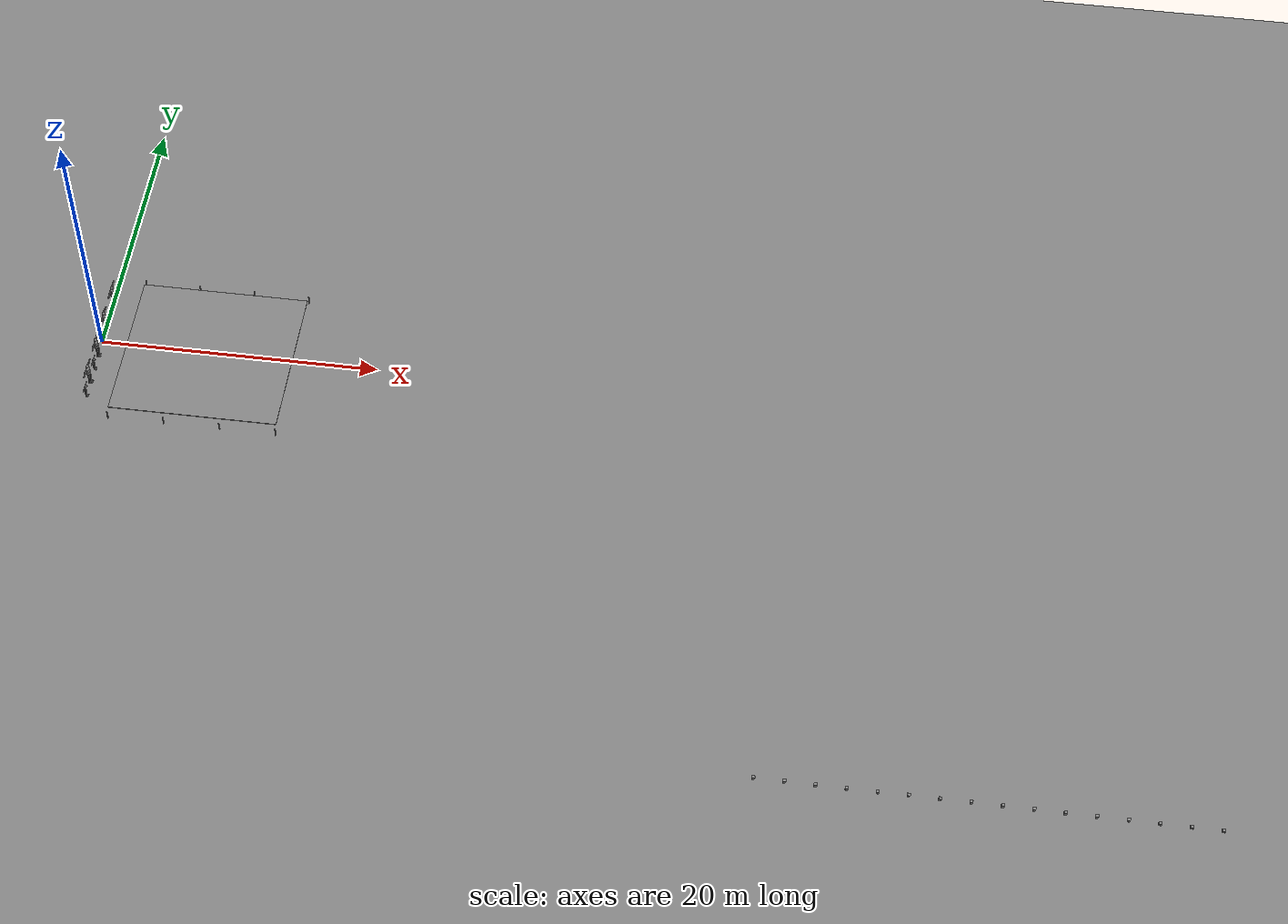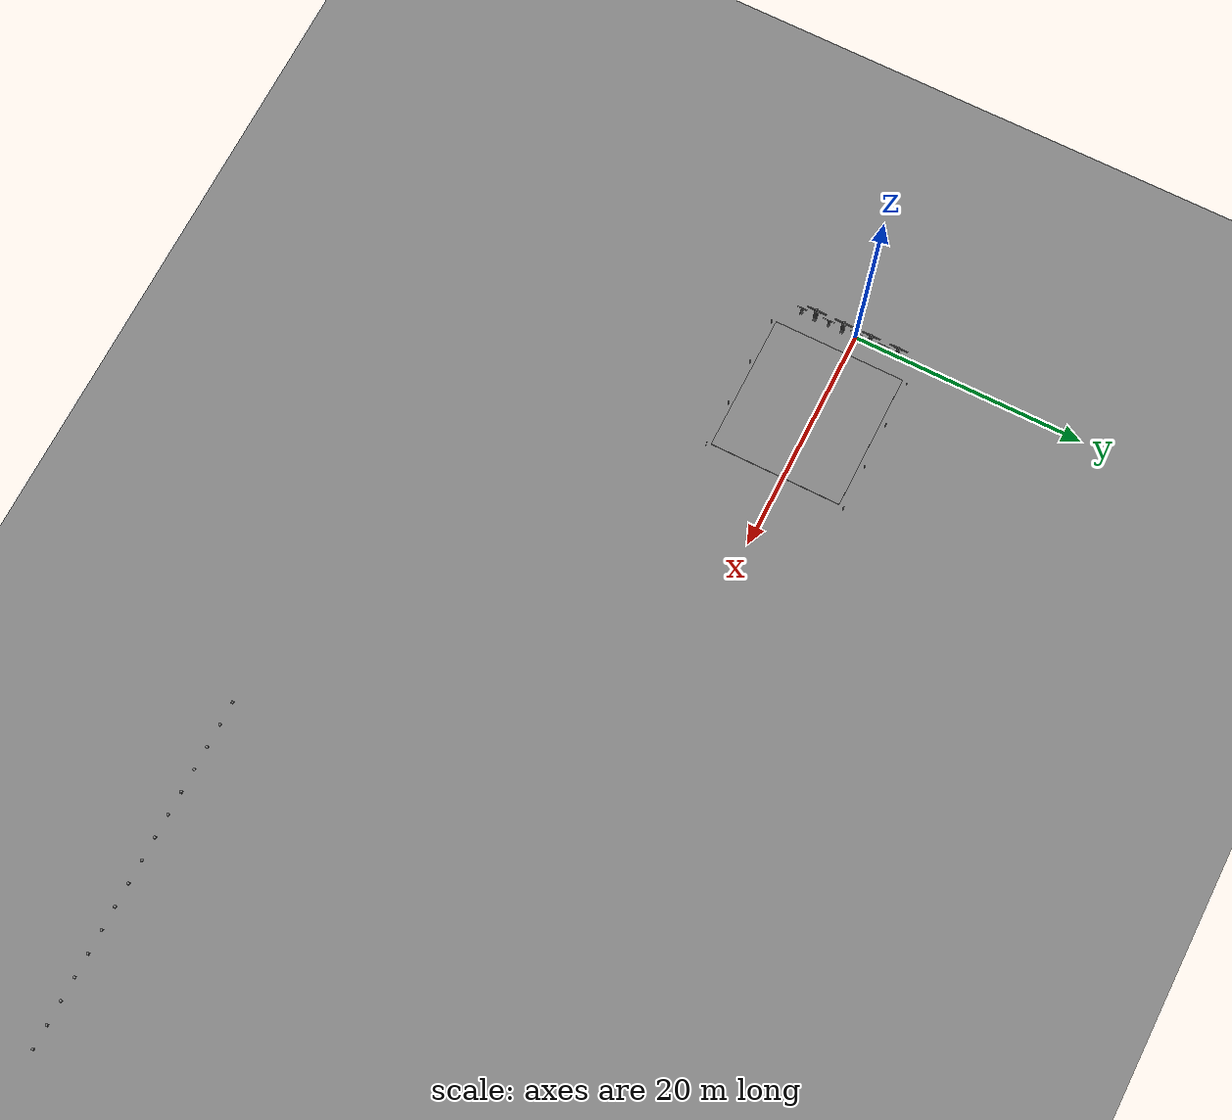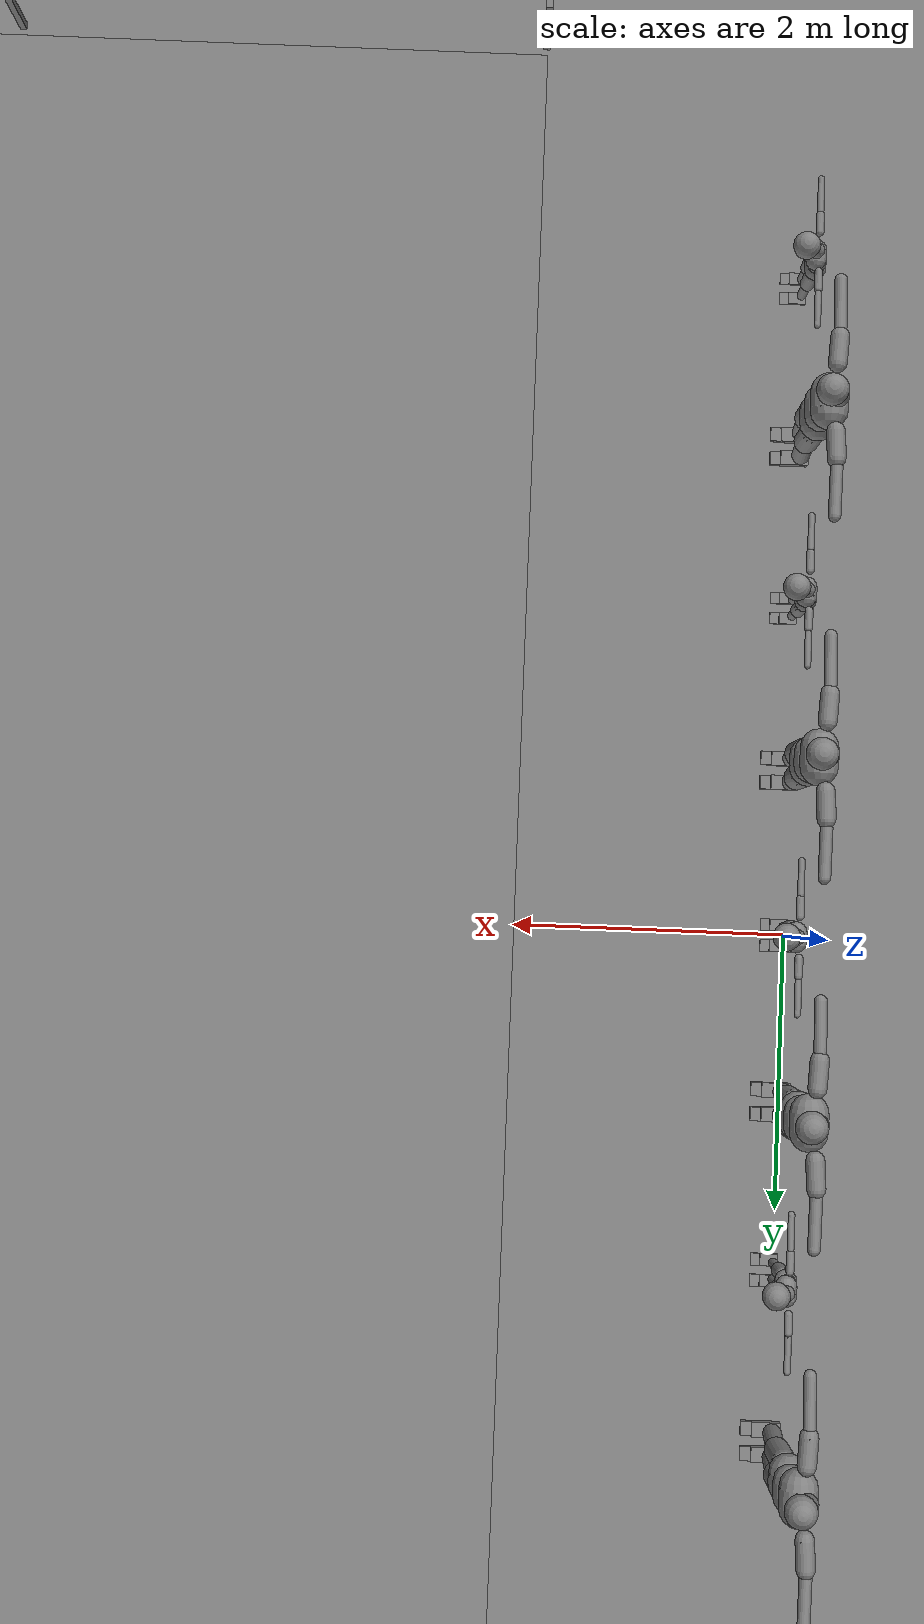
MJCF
<!-- GENERATED by training/tools/compose_mixed.py (trench8, lineup matt,zombie,matt,zombie,matt,zombie,matt,zombie). Do not edit. -->
<mujoco model="trench8_mixed">
  <compiler angle="degree" autolimits="true" />
  <option timestep="0.005" gravity="0 0 -9.81" integrator="implicitfast" solver="Newton" iterations="20" cone="pyramidal" jacobian="auto">
    <flag multiccd="disable" />
  </option>
  <worldbody>
    <light name="sun" pos="0 0 5" dir="0 0 -1" directional="true" />
    <geom name="ground" type="plane" size="0 0 0.05" contype="65535" conaffinity="65535" condim="3" friction="1 0.005 0.0001" />
    <geom name="trench_ceiling" type="box" pos="8 -0.61 0.74" size="6 5.68 0.02" contype="65535" conaffinity="65535" condim="3" friction="1 0.005 0.0001" />
    <geom name="trench_post0_0" type="box" pos="2 -6.69 0.36" size="0.025 0.025 0.36" contype="65535" conaffinity="65535" condim="3" friction="1 0.005 0.0001" />
    <geom name="trench_post0_1" type="box" pos="6 -6.69 0.36" size="0.025 0.025 0.36" contype="65535" conaffinity="65535" condim="3" friction="1 0.005 0.0001" />
    <geom name="trench_post0_2" type="box" pos="10 -6.69 0.36" size="0.025 0.025 0.36" contype="65535" conaffinity="65535" condim="3" friction="1 0.005 0.0001" />
    <geom name="trench_post0_3" type="box" pos="14 -6.69 0.36" size="0.025 0.025 0.36" contype="65535" conaffinity="65535" condim="3" friction="1 0.005 0.0001" />
    <geom name="trench_post1_0" type="box" pos="2 5.47 0.36" size="0.025 0.025 0.36" contype="65535" conaffinity="65535" condim="3" friction="1 0.005 0.0001" />
    <geom name="trench_post1_1" type="box" pos="6 5.47 0.36" size="0.025 0.025 0.36" contype="65535" conaffinity="65535" condim="3" friction="1 0.005 0.0001" />
    <geom name="trench_post1_2" type="box" pos="10 5.47 0.36" size="0.025 0.025 0.36" contype="65535" conaffinity="65535" condim="3" friction="1 0.005 0.0001" />
    <geom name="trench_post1_3" type="box" pos="14 5.47 0.36" size="0.025 0.025 0.36" contype="65535" conaffinity="65535" condim="3" friction="1 0.005 0.0001" />
    <body name="L0_pelvis" pos="0.014059 3.66 0.966775">
      <inertial pos="-0.01696645 0 -0.003757688" quat="0.7071068 -0.7071068 0 0" mass="8.937766" diaginertia="0.0907144 0.0907144 0.07049761" />
      <freejoint name="L0_root" />
      <geom name="L0_pelvis_geom0" type="capsule" size="0.1357963 0.03473648" contype="65537" conaffinity="16646144" condim="3" friction="1 0.005 0.0001" pos="-0.01696645 0 -0.003757688" quat="0.7071068 -0.7071068 0 0" />
      <body name="L0_torso" pos="-0.000796 0 0.095775">
        <inertial pos="0.003384799 0 0.1412323" quat="0.7071068 -0.7071068 0 0" mass="13.05674" diaginertia="0.1165244 0.1165244 0.08048442" />
        <joint name="L0_abdomen_flex" type="hinge" pos="0 0 0" axis="0 1 0" range="-30 60" armature="0.02" />
        <joint name="L0_abdomen_lat" type="hinge" pos="0 0 0" axis="1 0 0" range="-35 35" armature="0.02" />
        <joint name="L0_abdomen_twist" type="hinge" pos="0 0 0" axis="0 0 1" range="-45 45" armature="0.02" />
        <geom name="L0_torso_geom0" type="capsule" size="0.1189253 0.04429121" contype="65537" conaffinity="16646144" condim="3" friction="1 0.005 0.0001" pos="0.003384799 0 0.1412323" quat="0.7071068 -0.7071068 0 0" />
        <body name="L0_chest" pos="-0.016728 0 0.279754">
          <inertial pos="-0.003824043 0 0.05326067" quat="0.7071068 -0.7071068 0 0" mass="12.76681" diaginertia="0.157376 0.157376 0.09756839" />
          <geom name="L0_chest_geom0" type="capsule" size="0.1315126 0.06314432" contype="65537" conaffinity="16646144" condim="3" friction="1 0.005 0.0001" pos="-0.003824043 0 0.05326067" quat="0.7071068 -0.7071068 0 0" />
          <body name="L0_head" pos="-0.048542 0 0.181344">
            <inertial pos="0.05070428 0 0.1332104" quat="0.6920062 0.1453527 0.1453527 0.6920062" mass="5.548613" diaginertia="0.0503217 0.05005417 0.02171975" />
            <geom name="L0_head_geom0" type="capsule" size="0.06994246 0.0600033" contype="65537" conaffinity="16646144" condim="3" friction="1 0.005 0.0001" pos="0.013404 0 0.058487" quat="0.9936623 0 0.1124062 0" />
            <geom name="L0_head_geom1" type="sphere" size="0.1098854" contype="65537" conaffinity="16646144" condim="3" friction="1 0.005 0.0001" pos="0.07270066 0 0.1772756" />
          </body>
          <body name="L0_upper_arm_l" pos="-0.033514 0.201796 0.161482">
            <inertial pos="-0.007092 0.126 0.00073" quat="0.7091489 -0.7039445 -0.03962202 0" mass="2.169458" diaginertia="0.01610463 0.01610463 0.004156322" />
            <joint name="L0_shoulder_elev_l" type="hinge" pos="0 0 0" axis="1 0 0" range="-95 80" armature="0.01" />
            <joint name="L0_shoulder_flex_l" type="hinge" pos="0 0 0" axis="0 0 -1" range="-60 170" armature="0.01" />
            <joint name="L0_shoulder_twist_l" type="hinge" pos="0 0 0" axis="0 1 0" range="-80 80" armature="0.01" />
            <geom name="L0_upper_arm_l_geom0" type="capsule" size="0.06392297 0.09424006" contype="65537" conaffinity="16646144" condim="3" friction="1 0.005 0.0001" pos="-0.007092 0.126 0.00073" quat="0.7091489 -0.7039445 -0.03962202 0" />
            <body name="L0_forearm_l" pos="-0.014184 0.252 0.00146">
              <inertial pos="0.0027005 0.1902425 -0.00161" quat="0.7041088 -0.7100206 0.01007877 0" mass="1.789553" diaginertia="0.02422419 0.02422419 0.001594476" />
              <joint name="L0_elbow_l" type="hinge" pos="0 0 0" axis="0 0 -1" range="0 145" armature="0.01" />
              <geom name="L0_forearm_l_geom0" type="capsule" size="0.04283781 0.1688496" contype="65537" conaffinity="16646144" condim="3" friction="1 0.005 0.0001" pos="0.0027005 0.1902425 -0.00161" quat="0.7041088 -0.7100206 0.01007877 0" />
            </body>
          </body>
          <body name="L0_upper_arm_r" pos="-0.033514 -0.201796 0.161482">
            <inertial pos="-0.007092 -0.126 0.00073" quat="0.7091489 0.7039445 -0.03962202 0" mass="2.169458" diaginertia="0.01610463 0.01610463 0.004156322" />
            <joint name="L0_shoulder_elev_r" type="hinge" pos="0 0 0" axis="-1 0 0" range="-95 80" armature="0.01" />
            <joint name="L0_shoulder_flex_r" type="hinge" pos="0 0 0" axis="0 0 1" range="-60 170" armature="0.01" />
            <joint name="L0_shoulder_twist_r" type="hinge" pos="0 0 0" axis="0 1 0" range="-80 80" armature="0.01" />
            <geom name="L0_upper_arm_r_geom0" type="capsule" size="0.06392297 0.09424006" contype="65537" conaffinity="16646144" condim="3" friction="1 0.005 0.0001" pos="-0.007092 -0.126 0.00073" quat="0.7091489 0.7039445 -0.03962202 0" />
            <body name="L0_forearm_r" pos="-0.014184 -0.252 0.00146">
              <inertial pos="0.0027005 -0.1902425 -0.00161" quat="0.7041088 0.7100206 0.01007877 0" mass="1.789553" diaginertia="0.02422419 0.02422419 0.001594476" />
              <joint name="L0_elbow_r" type="hinge" pos="0 0 0" axis="0 0 1" range="0 145" armature="0.01" />
              <geom name="L0_forearm_r_geom0" type="capsule" size="0.04283781 0.1688496" contype="65537" conaffinity="16646144" condim="3" friction="1 0.005 0.0001" pos="0.0027005 -0.1902425 -0.00161" quat="0.7041088 0.7100206 0.01007877 0" />
            </body>
          </body>
        </body>
      </body>
      <body name="L0_thigh_l" pos="0.000827 0.085706 -0.03016">
        <inertial pos="0.002864 0 -0.207727" quat="0.006893172 0 0.9999762 0" mass="11.32717" diaginertia="0.2130858 0.2130858 0.04235914" />
        <joint name="L0_hip_flex_l" type="hinge" pos="0 0 0" axis="0 -1 0" range="-30 120" armature="0.02" />
        <joint name="L0_hip_abd_l" type="hinge" pos="0 0 0" axis="1 0 0" range="-30 45" armature="0.02" />
        <joint name="L0_hip_rot_l" type="hinge" pos="0 0 0" axis="0 0 1" range="-40 40" armature="0.02" />
        <geom name="L0_thigh_l_geom0" type="capsule" size="0.08888116 0.1633062" contype="65792" conaffinity="16646400" condim="3" friction="1 0.005 0.0001" pos="0.002864 0 -0.207727" quat="0.006893172 0 0.9999762 0" />
        <body name="L0_shin_l" pos="0.005728 0 -0.415454">
          <inertial pos="-0.0159655 0 -0.214853" quat="0.03707781 0 -0.9993124 0" mass="3.459135" diaginertia="0.06386931 0.06386931 0.007533594" />
          <joint name="L0_knee_l" type="hinge" pos="0 0 0" axis="0 1 0" range="0 150" armature="0.02" />
          <geom name="L0_shin_l_geom0" type="capsule" size="0.06734565 0.1817725" contype="65792" conaffinity="16646400" condim="3" friction="1 0.005 0.0001" pos="-0.0159655 0 -0.214853" quat="0.03707781 0 -0.9993124 0" />
          <body name="L0_foot_l" pos="-0.031931 0 -0.429706">
            <inertial pos="0.03774256 0.002908948 -0.06798844" quat="1 0 0 0" mass="0.8497876" diaginertia="0.00103675 0.003237029 0.003763906" />
            <joint name="L0_ankle_dorsi_l" type="hinge" pos="0 0 0" axis="0 -1 0" range="-50 25" armature="0.01" />
            <joint name="L0_ankle_inv_l" type="hinge" pos="0 0 0" axis="-1 0 0" range="-20 30" armature="0.01" />
            <geom name="L0_foot_l_geom0" type="box" size="0.1026044 0.05253602 0.03" contype="65792" conaffinity="16646400" condim="3" friction="1 0.005 0.0001" pos="0.03774256 0.002908948 -0.06798844" />
            <body name="L0_toe_l" pos="0.140347 0 -0.07597">
              <inertial pos="0.03863281 0.004919875 -0.004518435" quat="1 0 0 0" mass="0.2499375" diaginertia="0.0002352078 0.0001498579 0.0003340368" />
              <joint name="L0_toe_l" type="hinge" pos="0 0 0" axis="0 -1 0" range="-30 60" stiffness="20" damping="1" armature="0.005" />
              <geom name="L0_toe_l_geom0" type="box" size="0.03863281 0.05016921 0.0175" contype="65792" conaffinity="16646400" condim="3" friction="1 0.005 0.0001" pos="0.03863281 0.004919875 -0.004518435" />
            </body>
          </body>
        </body>
      </body>
      <body name="L0_thigh_r" pos="0.000827 -0.085706 -0.03016">
        <inertial pos="0.002864 0 -0.207727" quat="0.006893172 0 0.9999762 0" mass="11.32717" diaginertia="0.2130858 0.2130858 0.04235914" />
        <joint name="L0_hip_flex_r" type="hinge" pos="0 0 0" axis="0 -1 0" range="-30 120" armature="0.02" />
        <joint name="L0_hip_abd_r" type="hinge" pos="0 0 0" axis="-1 0 0" range="-30 45" armature="0.02" />
        <joint name="L0_hip_rot_r" type="hinge" pos="0 0 0" axis="0 0 -1" range="-40 40" armature="0.02" />
        <geom name="L0_thigh_r_geom0" type="capsule" size="0.08888116 0.1633062" contype="65792" conaffinity="16646400" condim="3" friction="1 0.005 0.0001" pos="0.002864 0 -0.207727" quat="0.006893172 0 0.9999762 0" />
        <body name="L0_shin_r" pos="0.005728 0 -0.415454">
          <inertial pos="-0.0159655 0 -0.214853" quat="0.03707781 0 -0.9993124 0" mass="3.459135" diaginertia="0.06386931 0.06386931 0.007533594" />
          <joint name="L0_knee_r" type="hinge" pos="0 0 0" axis="0 1 0" range="0 150" armature="0.02" />
          <geom name="L0_shin_r_geom0" type="capsule" size="0.06734565 0.1817725" contype="65792" conaffinity="16646400" condim="3" friction="1 0.005 0.0001" pos="-0.0159655 0 -0.214853" quat="0.03707781 0 -0.9993124 0" />
          <body name="L0_foot_r" pos="-0.031931 0 -0.429706">
            <inertial pos="0.03774256 -0.002908948 -0.06798844" quat="1 0 0 0" mass="0.8497876" diaginertia="0.00103675 0.003237029 0.003763906" />
            <joint name="L0_ankle_dorsi_r" type="hinge" pos="0 0 0" axis="0 -1 0" range="-50 25" armature="0.01" />
            <joint name="L0_ankle_inv_r" type="hinge" pos="0 0 0" axis="1 0 0" range="-20 30" armature="0.01" />
            <geom name="L0_foot_r_geom0" type="box" size="0.1026044 0.05253602 0.03" contype="65792" conaffinity="16646400" condim="3" friction="1 0.005 0.0001" pos="0.03774256 -0.002908948 -0.06798844" />
            <body name="L0_toe_r" pos="0.140343 0 -0.075843">
              <inertial pos="0.03863281 -0.004919875 -0.004518435" quat="1 0 0 0" mass="0.2499375" diaginertia="0.0002352078 0.0001498579 0.0003340368" />
              <joint name="L0_toe_r" type="hinge" pos="0 0 0" axis="0 -1 0" range="-30 60" stiffness="20" damping="1" armature="0.005" />
              <geom name="L0_toe_r_geom0" type="box" size="0.03863281 0.05016921 0.0175" contype="65792" conaffinity="16646400" condim="3" friction="1 0.005 0.0001" pos="0.03863681 -0.004919875 -0.004645435" />
            </body>
          </body>
        </body>
      </body>
    </body>
    <body name="L1_pelvis" pos="0 2.44 0.559887">
      <inertial pos="-0.007612123 0 0.009433847" quat="0.7071068 -0.7071068 0 0" mass="2.457886" diaginertia="0.009705657 0.009705657 0.006605976" />
      <freejoint name="L1_root" />
      <geom name="L1_pelvis_geom0" type="capsule" size="0.07844793 0.03035992" contype="131584" conaffinity="16581120" condim="3" friction="1 0.005 0.0001" pos="-0.007612123 0 0.009433847" quat="0.7071068 -0.7071068 0 0" />
      <body name="L1_torso" pos="-0.001231 -2.6e-05 0.062415">
        <inertial pos="-0.005324366 2.6e-05 0.03596058" quat="0.7071068 -0.7071068 0 0" mass="3.590602" diaginertia="0.009810929 0.009810929 0.006378186" />
        <joint name="L1_abdomen_flex" type="hinge" pos="0 0 0" axis="0 1 0" range="-30 60" armature="0.002099598" />
        <joint name="L1_abdomen_lat" type="hinge" pos="0 0 0" axis="1 0 0" range="-35 35" armature="0.002099598" />
        <joint name="L1_abdomen_twist" type="hinge" pos="0 0 0" axis="0 0 1" range="-45 45" armature="0.002099598" />
        <geom name="L1_torso_geom0" type="capsule" size="0.06358528 0.02750999" contype="131584" conaffinity="16581120" condim="3" friction="1 0.005 0.0001" pos="-0.005324366 2.6e-05 0.03596058" quat="0.7071068 -0.7071068 0 0" />
        <body name="L1_chest" pos="-0.000412 0 0.109225">
          <inertial pos="0.02102744 2.6e-05 0.05248355" quat="0.7071068 -0.7071068 0 0" mass="3.510872" diaginertia="0.01368155 0.01368155 0.008567377" />
          <geom name="L1_chest_geom0" type="capsule" size="0.07435712 0.03495606" contype="131584" conaffinity="16581120" condim="3" friction="1 0.005 0.0001" pos="0.02102744 2.6e-05 0.05248355" quat="0.7071068 -0.7071068 0 0" />
          <body name="L1_head" pos="0.033148 0 0.156037">
            <inertial pos="0.06573305 1.878749e-05 0.0784395" quat="0.6614595 0.2478298 0.2473417 0.6632298" mass="1.525869" diaginertia="0.008143213 0.008139096 0.004756541" />
            <geom name="L1_head_geom0" type="capsule" size="0.05753786 0.03165845" contype="131584" conaffinity="16581120" condim="3" friction="1 0.005 0.0001" pos="0.018568 0 0.0256415" quat="0.9512996 0 0.3082679 0" />
            <geom name="L1_head_geom1" type="sphere" size="0.09675238" contype="131584" conaffinity="16581120" condim="3" friction="1 0.005 0.0001" pos="0.08383968 2.6e-05 0.09870861" />
          </body>
          <body name="L1_upper_arm_l" pos="0.009612 0.129445 0.124194">
            <inertial pos="-0.000137 0.078008 7.7e-05" quat="0.7074557 -0.7067566 -0.001241227 0" mass="0.5966008" diaginertia="0.001505767 0.001505767 0.0002328844" />
            <joint name="L1_shoulder_elev_l" type="hinge" pos="0 0 0" axis="1 0 0" range="-95 80" armature="0.001049799" />
            <joint name="L1_shoulder_flex_l" type="hinge" pos="0 0 0" axis="0 0 -1" range="-60 170" armature="0.001049799" />
            <joint name="L1_shoulder_twist_l" type="hinge" pos="0 0 0" axis="0 1 0" range="-80 80" armature="0.001049799" />
            <geom name="L1_upper_arm_l_geom0" type="capsule" size="0.028608 0.06370416" contype="131584" conaffinity="16581120" condim="3" friction="1 0.005 0.0001" pos="-0.000137 0.078008 7.7e-05" quat="0.7074557 -0.7067566 -0.001241227 0" />
            <body name="L1_forearm_l" pos="-0.000274 0.156016 0.000154">
              <inertial pos="9.064547e-05 0.1302764 3.230928e-05" quat="0.7071945 -0.7070189 0.0004919392 0" mass="0.492127" diaginertia="0.003034748 0.003034748 0.0001322193" />
              <joint name="L1_elbow_l" type="hinge" pos="0 0 0" axis="0 0 -1" range="0 145" armature="0.001049799" />
              <geom name="L1_forearm_l_geom0" type="capsule" size="0.0234555 0.1185487" contype="131584" conaffinity="16581120" condim="3" friction="1 0.005 0.0001" pos="9.064547e-05 0.1302764 3.230928e-05" quat="0.7071945 -0.7070189 0.0004919392 0" />
            </body>
          </body>
          <body name="L1_upper_arm_r" pos="0.009612 -0.129445 0.124194">
            <inertial pos="-0.000137 -0.078008 7.7e-05" quat="0.7074557 0.7067566 -0.001241227 0" mass="0.5966008" diaginertia="0.001505767 0.001505767 0.0002328844" />
            <joint name="L1_shoulder_elev_r" type="hinge" pos="0 0 0" axis="-1 0 0" range="-95 80" armature="0.001049799" />
            <joint name="L1_shoulder_flex_r" type="hinge" pos="0 0 0" axis="0 0 1" range="-60 170" armature="0.001049799" />
            <joint name="L1_shoulder_twist_r" type="hinge" pos="0 0 0" axis="0 1 0" range="-80 80" armature="0.001049799" />
            <geom name="L1_upper_arm_r_geom0" type="capsule" size="0.028608 0.06370416" contype="131584" conaffinity="16581120" condim="3" friction="1 0.005 0.0001" pos="-0.000137 -0.077956 7.7e-05" quat="0.7074557 0.7067566 -0.001241227 0" />
            <body name="L1_forearm_r" pos="-0.000271 -0.156311 0.000154">
              <inertial pos="9.064547e-05 -0.1302764 3.230928e-05" quat="0.7071945 0.7070189 0.0004919392 0" mass="0.492127" diaginertia="0.003034748 0.003034748 0.0001322193" />
              <joint name="L1_elbow_r" type="hinge" pos="0 0 0" axis="0 0 1" range="0 145" armature="0.001049799" />
              <geom name="L1_forearm_r_geom0" type="capsule" size="0.0234555 0.1185487" contype="131584" conaffinity="16581120" condim="3" friction="1 0.005 0.0001" pos="8.764547e-05 -0.1299294 3.230928e-05" quat="0.7071945 0.7070189 0.0004919392 0" />
            </body>
          </body>
        </body>
      </body>
      <body name="L1_thigh_l" pos="0.006255 0.0602 -0.015578">
        <inertial pos="0 0 -0.1278905" quat="0 1 0 0" mass="3.114971" diaginertia="0.02209944 0.02209944 0.004297472" />
        <joint name="L1_hip_flex_l" type="hinge" pos="0 0 0" axis="0 -1 0" range="-30 120" armature="0.002099598" />
        <joint name="L1_hip_abd_l" type="hinge" pos="0 0 0" axis="1 0 0" range="-30 45" armature="0.002099598" />
        <joint name="L1_hip_rot_l" type="hinge" pos="0 0 0" axis="0 0 1" range="-40 40" armature="0.002099598" />
        <geom name="L1_thigh_l_geom0" type="capsule" size="0.05396597 0.1009075" contype="131584" conaffinity="16581120" condim="3" friction="1 0.005 0.0001" pos="0 0 -0.1278905" quat="0 1 0 0" />
        <body name="L1_shin_l" pos="0 0 -0.255781">
          <inertial pos="0 0 -0.1340565" quat="0 1 0 0" mass="0.9512622" diaginertia="0.006572025 0.006572025 0.0005829297" />
          <joint name="L1_knee_l" type="hinge" pos="0 0 0" axis="0 1 0" range="0 150" armature="0.002099598" />
          <geom name="L1_shin_l_geom0" type="capsule" size="0.03561781 0.1162476" contype="131584" conaffinity="16581120" condim="3" friction="1 0.005 0.0001" pos="0 0 -0.1340565" quat="0 1 0 0" />
          <body name="L1_foot_l" pos="0 0 -0.268113">
            <inertial pos="0.02989977 0.01554355 -0.02697956" quat="1 0 0 0" mass="0.2336916" diaginertia="0.0001722914 0.000345643 0.000464408" />
            <joint name="L1_ankle_dorsi_l" type="hinge" pos="0 0 0" axis="0 -1 0" range="-50 25" armature="0.001049799" />
            <joint name="L1_ankle_inv_l" type="hinge" pos="0 0 0" axis="-1 0 0" range="-20 30" armature="0.001049799" />
            <geom name="L1_foot_l_geom0" type="box" size="0.06398123 0.04322278 0.01853566" contype="131584" conaffinity="16581120" condim="3" friction="1 0.005 0.0001" pos="0.02989977 0.01554355 -0.02697956" />
            <body name="L1_toe_l" pos="0.093881 0.002417 -0.028506">
              <inertial pos="0.03375064 0.01336441 -0.006196754" quat="1 0 0 0" mass="0.06873282" diaginertia="4.657589e-05 2.877649e-05 6.999537e-05" />
              <joint name="L1_toe_l" type="hinge" pos="0 0 0" axis="0 -1 0" range="-30 60" stiffness="3.398204" damping="0.1335558" armature="0.0005248994" />
              <geom name="L1_toe_l_geom0" type="box" size="0.03375064 0.04377215 0.01081247" contype="131584" conaffinity="16581120" condim="3" friction="1 0.005 0.0001" pos="0.03375064 0.01336441 -0.006196754" />
            </body>
          </body>
        </body>
      </body>
      <body name="L1_thigh_r" pos="0.006255 -0.060187 -0.015628">
        <inertial pos="0 0 -0.1278905" quat="0 -1 0 0" mass="3.114971" diaginertia="0.02209944 0.02209944 0.004297472" />
        <joint name="L1_hip_flex_r" type="hinge" pos="0 0 0" axis="0 -1 0" range="-30 120" armature="0.002099598" />
        <joint name="L1_hip_abd_r" type="hinge" pos="0 0 0" axis="-1 0 0" range="-30 45" armature="0.002099598" />
        <joint name="L1_hip_rot_r" type="hinge" pos="0 0 0" axis="0 0 -1" range="-40 40" armature="0.002099598" />
        <geom name="L1_thigh_r_geom0" type="capsule" size="0.05396597 0.1009075" contype="131584" conaffinity="16581120" condim="3" friction="1 0.005 0.0001" pos="0 -1.3e-05 -0.1278405" quat="0 1 0 0" />
        <body name="L1_shin_r" pos="0 0 -0.252279">
          <inertial pos="0 0 -0.1340565" quat="0 -1 0 0" mass="0.9512622" diaginertia="0.006572025 0.006572025 0.0005829297" />
          <joint name="L1_knee_r" type="hinge" pos="0 0 0" axis="0 1 0" range="0 150" armature="0.002099598" />
          <geom name="L1_shin_r_geom0" type="capsule" size="0.03561781 0.1162476" contype="131584" conaffinity="16581120" condim="3" friction="1 0.005 0.0001" pos="0 -1.3e-05 -0.1375085" quat="0 1 0 0" />
          <body name="L1_foot_r" pos="0 0 -0.269013">
            <inertial pos="0.02989977 -0.01554355 -0.02697956" quat="1 0 0 0" mass="0.2336916" diaginertia="0.0001722914 0.000345643 0.000464408" />
            <joint name="L1_ankle_dorsi_r" type="hinge" pos="0 0 0" axis="0 -1 0" range="-50 25" armature="0.001049799" />
            <joint name="L1_ankle_inv_r" type="hinge" pos="0 0 0" axis="1 0 0" range="-20 30" armature="0.001049799" />
            <geom name="L1_foot_r_geom0" type="box" size="0.06398123 0.04322278 0.01853566" contype="131584" conaffinity="16581120" condim="3" friction="1 0.005 0.0001" pos="0.02989977 -0.01555655 -0.02953156" />
            <body name="L1_toe_r" pos="0.089318 -0.003451 -0.028805">
              <inertial pos="0.03375064 -0.01336441 -0.006196754" quat="1 0 0 0" mass="0.06873282" diaginertia="4.657589e-05 2.877649e-05 6.999537e-05" />
              <joint name="L1_toe_r" type="hinge" pos="0 0 0" axis="0 -1 0" range="-30 60" stiffness="3.398204" damping="0.1335558" armature="0.0005248994" />
              <geom name="L1_toe_r_geom0" type="box" size="0.03375064 0.04377215 0.01081247" contype="131584" conaffinity="16581120" condim="3" friction="1 0.005 0.0001" pos="0.03831364 -0.01234341 -0.008449754" />
            </body>
          </body>
        </body>
      </body>
    </body>
    <body name="L2_pelvis" pos="0.014059 1.22 0.966775">
      <inertial pos="-0.01696645 0 -0.003757688" quat="0.7071068 -0.7071068 0 0" mass="8.937766" diaginertia="0.0907144 0.0907144 0.07049761" />
      <freejoint name="L2_root" />
      <geom name="L2_pelvis_geom0" type="capsule" size="0.1357963 0.03473648" contype="262148" conaffinity="16449536" condim="3" friction="1 0.005 0.0001" pos="-0.01696645 0 -0.003757688" quat="0.7071068 -0.7071068 0 0" />
      <body name="L2_torso" pos="-0.000796 0 0.095775">
        <inertial pos="0.003384799 0 0.1412323" quat="0.7071068 -0.7071068 0 0" mass="13.05674" diaginertia="0.1165244 0.1165244 0.08048442" />
        <joint name="L2_abdomen_flex" type="hinge" pos="0 0 0" axis="0 1 0" range="-30 60" armature="0.02" />
        <joint name="L2_abdomen_lat" type="hinge" pos="0 0 0" axis="1 0 0" range="-35 35" armature="0.02" />
        <joint name="L2_abdomen_twist" type="hinge" pos="0 0 0" axis="0 0 1" range="-45 45" armature="0.02" />
        <geom name="L2_torso_geom0" type="capsule" size="0.1189253 0.04429121" contype="262148" conaffinity="16449536" condim="3" friction="1 0.005 0.0001" pos="0.003384799 0 0.1412323" quat="0.7071068 -0.7071068 0 0" />
        <body name="L2_chest" pos="-0.016728 0 0.279754">
          <inertial pos="-0.003824043 0 0.05326067" quat="0.7071068 -0.7071068 0 0" mass="12.76681" diaginertia="0.157376 0.157376 0.09756839" />
          <geom name="L2_chest_geom0" type="capsule" size="0.1315126 0.06314432" contype="262148" conaffinity="16449536" condim="3" friction="1 0.005 0.0001" pos="-0.003824043 0 0.05326067" quat="0.7071068 -0.7071068 0 0" />
          <body name="L2_head" pos="-0.048542 0 0.181344">
            <inertial pos="0.05070428 0 0.1332104" quat="0.6920062 0.1453527 0.1453527 0.6920062" mass="5.548613" diaginertia="0.0503217 0.05005417 0.02171975" />
            <geom name="L2_head_geom0" type="capsule" size="0.06994246 0.0600033" contype="262148" conaffinity="16449536" condim="3" friction="1 0.005 0.0001" pos="0.013404 0 0.058487" quat="0.9936623 0 0.1124062 0" />
            <geom name="L2_head_geom1" type="sphere" size="0.1098854" contype="262148" conaffinity="16449536" condim="3" friction="1 0.005 0.0001" pos="0.07270066 0 0.1772756" />
          </body>
          <body name="L2_upper_arm_l" pos="-0.033514 0.201796 0.161482">
            <inertial pos="-0.007092 0.126 0.00073" quat="0.7091489 -0.7039445 -0.03962202 0" mass="2.169458" diaginertia="0.01610463 0.01610463 0.004156322" />
            <joint name="L2_shoulder_elev_l" type="hinge" pos="0 0 0" axis="1 0 0" range="-95 80" armature="0.01" />
            <joint name="L2_shoulder_flex_l" type="hinge" pos="0 0 0" axis="0 0 -1" range="-60 170" armature="0.01" />
            <joint name="L2_shoulder_twist_l" type="hinge" pos="0 0 0" axis="0 1 0" range="-80 80" armature="0.01" />
            <geom name="L2_upper_arm_l_geom0" type="capsule" size="0.06392297 0.09424006" contype="262148" conaffinity="16449536" condim="3" friction="1 0.005 0.0001" pos="-0.007092 0.126 0.00073" quat="0.7091489 -0.7039445 -0.03962202 0" />
            <body name="L2_forearm_l" pos="-0.014184 0.252 0.00146">
              <inertial pos="0.0027005 0.1902425 -0.00161" quat="0.7041088 -0.7100206 0.01007877 0" mass="1.789553" diaginertia="0.02422419 0.02422419 0.001594476" />
              <joint name="L2_elbow_l" type="hinge" pos="0 0 0" axis="0 0 -1" range="0 145" armature="0.01" />
              <geom name="L2_forearm_l_geom0" type="capsule" size="0.04283781 0.1688496" contype="262148" conaffinity="16449536" condim="3" friction="1 0.005 0.0001" pos="0.0027005 0.1902425 -0.00161" quat="0.7041088 -0.7100206 0.01007877 0" />
            </body>
          </body>
          <body name="L2_upper_arm_r" pos="-0.033514 -0.201796 0.161482">
            <inertial pos="-0.007092 -0.126 0.00073" quat="0.7091489 0.7039445 -0.03962202 0" mass="2.169458" diaginertia="0.01610463 0.01610463 0.004156322" />
            <joint name="L2_shoulder_elev_r" type="hinge" pos="0 0 0" axis="-1 0 0" range="-95 80" armature="0.01" />
            <joint name="L2_shoulder_flex_r" type="hinge" pos="0 0 0" axis="0 0 1" range="-60 170" armature="0.01" />
            <joint name="L2_shoulder_twist_r" type="hinge" pos="0 0 0" axis="0 1 0" range="-80 80" armature="0.01" />
            <geom name="L2_upper_arm_r_geom0" type="capsule" size="0.06392297 0.09424006" contype="262148" conaffinity="16449536" condim="3" friction="1 0.005 0.0001" pos="-0.007092 -0.126 0.00073" quat="0.7091489 0.7039445 -0.03962202 0" />
            <body name="L2_forearm_r" pos="-0.014184 -0.252 0.00146">
              <inertial pos="0.0027005 -0.1902425 -0.00161" quat="0.7041088 0.7100206 0.01007877 0" mass="1.789553" diaginertia="0.02422419 0.02422419 0.001594476" />
              <joint name="L2_elbow_r" type="hinge" pos="0 0 0" axis="0 0 1" range="0 145" armature="0.01" />
              <geom name="L2_forearm_r_geom0" type="capsule" size="0.04283781 0.1688496" contype="262148" conaffinity="16449536" condim="3" friction="1 0.005 0.0001" pos="0.0027005 -0.1902425 -0.00161" quat="0.7041088 0.7100206 0.01007877 0" />
            </body>
          </body>
        </body>
      </body>
      <body name="L2_thigh_l" pos="0.000827 0.085706 -0.03016">
        <inertial pos="0.002864 0 -0.207727" quat="0.006893172 0 0.9999762 0" mass="11.32717" diaginertia="0.2130858 0.2130858 0.04235914" />
        <joint name="L2_hip_flex_l" type="hinge" pos="0 0 0" axis="0 -1 0" range="-30 120" armature="0.02" />
        <joint name="L2_hip_abd_l" type="hinge" pos="0 0 0" axis="1 0 0" range="-30 45" armature="0.02" />
        <joint name="L2_hip_rot_l" type="hinge" pos="0 0 0" axis="0 0 1" range="-40 40" armature="0.02" />
        <geom name="L2_thigh_l_geom0" type="capsule" size="0.08888116 0.1633062" contype="263168" conaffinity="16450560" condim="3" friction="1 0.005 0.0001" pos="0.002864 0 -0.207727" quat="0.006893172 0 0.9999762 0" />
        <body name="L2_shin_l" pos="0.005728 0 -0.415454">
          <inertial pos="-0.0159655 0 -0.214853" quat="0.03707781 0 -0.9993124 0" mass="3.459135" diaginertia="0.06386931 0.06386931 0.007533594" />
          <joint name="L2_knee_l" type="hinge" pos="0 0 0" axis="0 1 0" range="0 150" armature="0.02" />
          <geom name="L2_shin_l_geom0" type="capsule" size="0.06734565 0.1817725" contype="263168" conaffinity="16450560" condim="3" friction="1 0.005 0.0001" pos="-0.0159655 0 -0.214853" quat="0.03707781 0 -0.9993124 0" />
          <body name="L2_foot_l" pos="-0.031931 0 -0.429706">
            <inertial pos="0.03774256 0.002908948 -0.06798844" quat="1 0 0 0" mass="0.8497876" diaginertia="0.00103675 0.003237029 0.003763906" />
            <joint name="L2_ankle_dorsi_l" type="hinge" pos="0 0 0" axis="0 -1 0" range="-50 25" armature="0.01" />
            <joint name="L2_ankle_inv_l" type="hinge" pos="0 0 0" axis="-1 0 0" range="-20 30" armature="0.01" />
            <geom name="L2_foot_l_geom0" type="box" size="0.1026044 0.05253602 0.03" contype="263168" conaffinity="16450560" condim="3" friction="1 0.005 0.0001" pos="0.03774256 0.002908948 -0.06798844" />
            <body name="L2_toe_l" pos="0.140347 0 -0.07597">
              <inertial pos="0.03863281 0.004919875 -0.004518435" quat="1 0 0 0" mass="0.2499375" diaginertia="0.0002352078 0.0001498579 0.0003340368" />
              <joint name="L2_toe_l" type="hinge" pos="0 0 0" axis="0 -1 0" range="-30 60" stiffness="20" damping="1" armature="0.005" />
              <geom name="L2_toe_l_geom0" type="box" size="0.03863281 0.05016921 0.0175" contype="263168" conaffinity="16450560" condim="3" friction="1 0.005 0.0001" pos="0.03863281 0.004919875 -0.004518435" />
            </body>
          </body>
        </body>
      </body>
      <body name="L2_thigh_r" pos="0.000827 -0.085706 -0.03016">
        <inertial pos="0.002864 0 -0.207727" quat="0.006893172 0 0.9999762 0" mass="11.32717" diaginertia="0.2130858 0.2130858 0.04235914" />
        <joint name="L2_hip_flex_r" type="hinge" pos="0 0 0" axis="0 -1 0" range="-30 120" armature="0.02" />
        <joint name="L2_hip_abd_r" type="hinge" pos="0 0 0" axis="-1 0 0" range="-30 45" armature="0.02" />
        <joint name="L2_hip_rot_r" type="hinge" pos="0 0 0" axis="0 0 -1" range="-40 40" armature="0.02" />
        <geom name="L2_thigh_r_geom0" type="capsule" size="0.08888116 0.1633062" contype="263168" conaffinity="16450560" condim="3" friction="1 0.005 0.0001" pos="0.002864 0 -0.207727" quat="0.006893172 0 0.9999762 0" />
        <body name="L2_shin_r" pos="0.005728 0 -0.415454">
          <inertial pos="-0.0159655 0 -0.214853" quat="0.03707781 0 -0.9993124 0" mass="3.459135" diaginertia="0.06386931 0.06386931 0.007533594" />
          <joint name="L2_knee_r" type="hinge" pos="0 0 0" axis="0 1 0" range="0 150" armature="0.02" />
          <geom name="L2_shin_r_geom0" type="capsule" size="0.06734565 0.1817725" contype="263168" conaffinity="16450560" condim="3" friction="1 0.005 0.0001" pos="-0.0159655 0 -0.214853" quat="0.03707781 0 -0.9993124 0" />
          <body name="L2_foot_r" pos="-0.031931 0 -0.429706">
            <inertial pos="0.03774256 -0.002908948 -0.06798844" quat="1 0 0 0" mass="0.8497876" diaginertia="0.00103675 0.003237029 0.003763906" />
            <joint name="L2_ankle_dorsi_r" type="hinge" pos="0 0 0" axis="0 -1 0" range="-50 25" armature="0.01" />
            <joint name="L2_ankle_inv_r" type="hinge" pos="0 0 0" axis="1 0 0" range="-20 30" armature="0.01" />
            <geom name="L2_foot_r_geom0" type="box" size="0.1026044 0.05253602 0.03" contype="263168" conaffinity="16450560" condim="3" friction="1 0.005 0.0001" pos="0.03774256 -0.002908948 -0.06798844" />
            <body name="L2_toe_r" pos="0.140343 0 -0.075843">
              <inertial pos="0.03863281 -0.004919875 -0.004518435" quat="1 0 0 0" mass="0.2499375" diaginertia="0.0002352078 0.0001498579 0.0003340368" />
              <joint name="L2_toe_r" type="hinge" pos="0 0 0" axis="0 -1 0" range="-30 60" stiffness="20" damping="1" armature="0.005" />
              <geom name="L2_toe_r_geom0" type="box" size="0.03863281 0.05016921 0.0175" contype="263168" conaffinity="16450560" condim="3" friction="1 0.005 0.0001" pos="0.03863681 -0.004919875 -0.004645435" />
            </body>
          </body>
        </body>
      </body>
    </body>
    <body name="L3_pelvis" pos="0 0 0.559887">
      <inertial pos="-0.007612123 0 0.009433847" quat="0.7071068 -0.7071068 0 0" mass="2.457886" diaginertia="0.009705657 0.009705657 0.006605976" />
      <freejoint name="L3_root" />
      <geom name="L3_pelvis_geom0" type="capsule" size="0.07844793 0.03035992" contype="526336" conaffinity="16189440" condim="3" friction="1 0.005 0.0001" pos="-0.007612123 0 0.009433847" quat="0.7071068 -0.7071068 0 0" />
      <body name="L3_torso" pos="-0.001231 -2.6e-05 0.062415">
        <inertial pos="-0.005324366 2.6e-05 0.03596058" quat="0.7071068 -0.7071068 0 0" mass="3.590602" diaginertia="0.009810929 0.009810929 0.006378186" />
        <joint name="L3_abdomen_flex" type="hinge" pos="0 0 0" axis="0 1 0" range="-30 60" armature="0.002099598" />
        <joint name="L3_abdomen_lat" type="hinge" pos="0 0 0" axis="1 0 0" range="-35 35" armature="0.002099598" />
        <joint name="L3_abdomen_twist" type="hinge" pos="0 0 0" axis="0 0 1" range="-45 45" armature="0.002099598" />
        <geom name="L3_torso_geom0" type="capsule" size="0.06358528 0.02750999" contype="526336" conaffinity="16189440" condim="3" friction="1 0.005 0.0001" pos="-0.005324366 2.6e-05 0.03596058" quat="0.7071068 -0.7071068 0 0" />
        <body name="L3_chest" pos="-0.000412 0 0.109225">
          <inertial pos="0.02102744 2.6e-05 0.05248355" quat="0.7071068 -0.7071068 0 0" mass="3.510872" diaginertia="0.01368155 0.01368155 0.008567377" />
          <geom name="L3_chest_geom0" type="capsule" size="0.07435712 0.03495606" contype="526336" conaffinity="16189440" condim="3" friction="1 0.005 0.0001" pos="0.02102744 2.6e-05 0.05248355" quat="0.7071068 -0.7071068 0 0" />
          <body name="L3_head" pos="0.033148 0 0.156037">
            <inertial pos="0.06573305 1.878749e-05 0.0784395" quat="0.6614595 0.2478298 0.2473417 0.6632298" mass="1.525869" diaginertia="0.008143213 0.008139096 0.004756541" />
            <geom name="L3_head_geom0" type="capsule" size="0.05753786 0.03165845" contype="526336" conaffinity="16189440" condim="3" friction="1 0.005 0.0001" pos="0.018568 0 0.0256415" quat="0.9512996 0 0.3082679 0" />
            <geom name="L3_head_geom1" type="sphere" size="0.09675238" contype="526336" conaffinity="16189440" condim="3" friction="1 0.005 0.0001" pos="0.08383968 2.6e-05 0.09870861" />
          </body>
          <body name="L3_upper_arm_l" pos="0.009612 0.129445 0.124194">
            <inertial pos="-0.000137 0.078008 7.7e-05" quat="0.7074557 -0.7067566 -0.001241227 0" mass="0.5966008" diaginertia="0.001505767 0.001505767 0.0002328844" />
            <joint name="L3_shoulder_elev_l" type="hinge" pos="0 0 0" axis="1 0 0" range="-95 80" armature="0.001049799" />
            <joint name="L3_shoulder_flex_l" type="hinge" pos="0 0 0" axis="0 0 -1" range="-60 170" armature="0.001049799" />
            <joint name="L3_shoulder_twist_l" type="hinge" pos="0 0 0" axis="0 1 0" range="-80 80" armature="0.001049799" />
            <geom name="L3_upper_arm_l_geom0" type="capsule" size="0.028608 0.06370416" contype="526336" conaffinity="16189440" condim="3" friction="1 0.005 0.0001" pos="-0.000137 0.078008 7.7e-05" quat="0.7074557 -0.7067566 -0.001241227 0" />
            <body name="L3_forearm_l" pos="-0.000274 0.156016 0.000154">
              <inertial pos="9.064547e-05 0.1302764 3.230928e-05" quat="0.7071945 -0.7070189 0.0004919392 0" mass="0.492127" diaginertia="0.003034748 0.003034748 0.0001322193" />
              <joint name="L3_elbow_l" type="hinge" pos="0 0 0" axis="0 0 -1" range="0 145" armature="0.001049799" />
              <geom name="L3_forearm_l_geom0" type="capsule" size="0.0234555 0.1185487" contype="526336" conaffinity="16189440" condim="3" friction="1 0.005 0.0001" pos="9.064547e-05 0.1302764 3.230928e-05" quat="0.7071945 -0.7070189 0.0004919392 0" />
            </body>
          </body>
          <body name="L3_upper_arm_r" pos="0.009612 -0.129445 0.124194">
            <inertial pos="-0.000137 -0.078008 7.7e-05" quat="0.7074557 0.7067566 -0.001241227 0" mass="0.5966008" diaginertia="0.001505767 0.001505767 0.0002328844" />
            <joint name="L3_shoulder_elev_r" type="hinge" pos="0 0 0" axis="-1 0 0" range="-95 80" armature="0.001049799" />
            <joint name="L3_shoulder_flex_r" type="hinge" pos="0 0 0" axis="0 0 1" range="-60 170" armature="0.001049799" />
            <joint name="L3_shoulder_twist_r" type="hinge" pos="0 0 0" axis="0 1 0" range="-80 80" armature="0.001049799" />
            <geom name="L3_upper_arm_r_geom0" type="capsule" size="0.028608 0.06370416" contype="526336" conaffinity="16189440" condim="3" friction="1 0.005 0.0001" pos="-0.000137 -0.077956 7.7e-05" quat="0.7074557 0.7067566 -0.001241227 0" />
            <body name="L3_forearm_r" pos="-0.000271 -0.156311 0.000154">
              <inertial pos="9.064547e-05 -0.1302764 3.230928e-05" quat="0.7071945 0.7070189 0.0004919392 0" mass="0.492127" diaginertia="0.003034748 0.003034748 0.0001322193" />
              <joint name="L3_elbow_r" type="hinge" pos="0 0 0" axis="0 0 1" range="0 145" armature="0.001049799" />
              <geom name="L3_forearm_r_geom0" type="capsule" size="0.0234555 0.1185487" contype="526336" conaffinity="16189440" condim="3" friction="1 0.005 0.0001" pos="8.764547e-05 -0.1299294 3.230928e-05" quat="0.7071945 0.7070189 0.0004919392 0" />
            </body>
          </body>
        </body>
      </body>
      <body name="L3_thigh_l" pos="0.006255 0.0602 -0.015578">
        <inertial pos="0 0 -0.1278905" quat="0 1 0 0" mass="3.114971" diaginertia="0.02209944 0.02209944 0.004297472" />
        <joint name="L3_hip_flex_l" type="hinge" pos="0 0 0" axis="0 -1 0" range="-30 120" armature="0.002099598" />
        <joint name="L3_hip_abd_l" type="hinge" pos="0 0 0" axis="1 0 0" range="-30 45" armature="0.002099598" />
        <joint name="L3_hip_rot_l" type="hinge" pos="0 0 0" axis="0 0 1" range="-40 40" armature="0.002099598" />
        <geom name="L3_thigh_l_geom0" type="capsule" size="0.05396597 0.1009075" contype="526336" conaffinity="16189440" condim="3" friction="1 0.005 0.0001" pos="0 0 -0.1278905" quat="0 1 0 0" />
        <body name="L3_shin_l" pos="0 0 -0.255781">
          <inertial pos="0 0 -0.1340565" quat="0 1 0 0" mass="0.9512622" diaginertia="0.006572025 0.006572025 0.0005829297" />
          <joint name="L3_knee_l" type="hinge" pos="0 0 0" axis="0 1 0" range="0 150" armature="0.002099598" />
          <geom name="L3_shin_l_geom0" type="capsule" size="0.03561781 0.1162476" contype="526336" conaffinity="16189440" condim="3" friction="1 0.005 0.0001" pos="0 0 -0.1340565" quat="0 1 0 0" />
          <body name="L3_foot_l" pos="0 0 -0.268113">
            <inertial pos="0.02989977 0.01554355 -0.02697956" quat="1 0 0 0" mass="0.2336916" diaginertia="0.0001722914 0.000345643 0.000464408" />
            <joint name="L3_ankle_dorsi_l" type="hinge" pos="0 0 0" axis="0 -1 0" range="-50 25" armature="0.001049799" />
            <joint name="L3_ankle_inv_l" type="hinge" pos="0 0 0" axis="-1 0 0" range="-20 30" armature="0.001049799" />
            <geom name="L3_foot_l_geom0" type="box" size="0.06398123 0.04322278 0.01853566" contype="526336" conaffinity="16189440" condim="3" friction="1 0.005 0.0001" pos="0.02989977 0.01554355 -0.02697956" />
            <body name="L3_toe_l" pos="0.093881 0.002417 -0.028506">
              <inertial pos="0.03375064 0.01336441 -0.006196754" quat="1 0 0 0" mass="0.06873282" diaginertia="4.657589e-05 2.877649e-05 6.999537e-05" />
              <joint name="L3_toe_l" type="hinge" pos="0 0 0" axis="0 -1 0" range="-30 60" stiffness="3.398204" damping="0.1335558" armature="0.0005248994" />
              <geom name="L3_toe_l_geom0" type="box" size="0.03375064 0.04377215 0.01081247" contype="526336" conaffinity="16189440" condim="3" friction="1 0.005 0.0001" pos="0.03375064 0.01336441 -0.006196754" />
            </body>
          </body>
        </body>
      </body>
      <body name="L3_thigh_r" pos="0.006255 -0.060187 -0.015628">
        <inertial pos="0 0 -0.1278905" quat="0 -1 0 0" mass="3.114971" diaginertia="0.02209944 0.02209944 0.004297472" />
        <joint name="L3_hip_flex_r" type="hinge" pos="0 0 0" axis="0 -1 0" range="-30 120" armature="0.002099598" />
        <joint name="L3_hip_abd_r" type="hinge" pos="0 0 0" axis="-1 0 0" range="-30 45" armature="0.002099598" />
        <joint name="L3_hip_rot_r" type="hinge" pos="0 0 0" axis="0 0 -1" range="-40 40" armature="0.002099598" />
        <geom name="L3_thigh_r_geom0" type="capsule" size="0.05396597 0.1009075" contype="526336" conaffinity="16189440" condim="3" friction="1 0.005 0.0001" pos="0 -1.3e-05 -0.1278405" quat="0 1 0 0" />
        <body name="L3_shin_r" pos="0 0 -0.252279">
          <inertial pos="0 0 -0.1340565" quat="0 -1 0 0" mass="0.9512622" diaginertia="0.006572025 0.006572025 0.0005829297" />
          <joint name="L3_knee_r" type="hinge" pos="0 0 0" axis="0 1 0" range="0 150" armature="0.002099598" />
          <geom name="L3_shin_r_geom0" type="capsule" size="0.03561781 0.1162476" contype="526336" conaffinity="16189440" condim="3" friction="1 0.005 0.0001" pos="0 -1.3e-05 -0.1375085" quat="0 1 0 0" />
          <body name="L3_foot_r" pos="0 0 -0.269013">
            <inertial pos="0.02989977 -0.01554355 -0.02697956" quat="1 0 0 0" mass="0.2336916" diaginertia="0.0001722914 0.000345643 0.000464408" />
            <joint name="L3_ankle_dorsi_r" type="hinge" pos="0 0 0" axis="0 -1 0" range="-50 25" armature="0.001049799" />
            <joint name="L3_ankle_inv_r" type="hinge" pos="0 0 0" axis="1 0 0" range="-20 30" armature="0.001049799" />
            <geom name="L3_foot_r_geom0" type="box" size="0.06398123 0.04322278 0.01853566" contype="526336" conaffinity="16189440" condim="3" friction="1 0.005 0.0001" pos="0.02989977 -0.01555655 -0.02953156" />
            <body name="L3_toe_r" pos="0.089318 -0.003451 -0.028805">
              <inertial pos="0.03375064 -0.01336441 -0.006196754" quat="1 0 0 0" mass="0.06873282" diaginertia="4.657589e-05 2.877649e-05 6.999537e-05" />
              <joint name="L3_toe_r" type="hinge" pos="0 0 0" axis="0 -1 0" range="-30 60" stiffness="3.398204" damping="0.1335558" armature="0.0005248994" />
              <geom name="L3_toe_r_geom0" type="box" size="0.03375064 0.04377215 0.01081247" contype="526336" conaffinity="16189440" condim="3" friction="1 0.005 0.0001" pos="0.03831364 -0.01234341 -0.008449754" />
            </body>
          </body>
        </body>
      </body>
    </body>
    <body name="L4_pelvis" pos="0.014059 -1.22 0.966775">
      <inertial pos="-0.01696645 0 -0.003757688" quat="0.7071068 -0.7071068 0 0" mass="8.937766" diaginertia="0.0907144 0.0907144 0.07049761" />
      <freejoint name="L4_root" />
      <geom name="L4_pelvis_geom0" type="capsule" size="0.1357963 0.03473648" contype="1048592" conaffinity="15663104" condim="3" friction="1 0.005 0.0001" pos="-0.01696645 0 -0.003757688" quat="0.7071068 -0.7071068 0 0" />
      <body name="L4_torso" pos="-0.000796 0 0.095775">
        <inertial pos="0.003384799 0 0.1412323" quat="0.7071068 -0.7071068 0 0" mass="13.05674" diaginertia="0.1165244 0.1165244 0.08048442" />
        <joint name="L4_abdomen_flex" type="hinge" pos="0 0 0" axis="0 1 0" range="-30 60" armature="0.02" />
        <joint name="L4_abdomen_lat" type="hinge" pos="0 0 0" axis="1 0 0" range="-35 35" armature="0.02" />
        <joint name="L4_abdomen_twist" type="hinge" pos="0 0 0" axis="0 0 1" range="-45 45" armature="0.02" />
        <geom name="L4_torso_geom0" type="capsule" size="0.1189253 0.04429121" contype="1048592" conaffinity="15663104" condim="3" friction="1 0.005 0.0001" pos="0.003384799 0 0.1412323" quat="0.7071068 -0.7071068 0 0" />
        <body name="L4_chest" pos="-0.016728 0 0.279754">
          <inertial pos="-0.003824043 0 0.05326067" quat="0.7071068 -0.7071068 0 0" mass="12.76681" diaginertia="0.157376 0.157376 0.09756839" />
          <geom name="L4_chest_geom0" type="capsule" size="0.1315126 0.06314432" contype="1048592" conaffinity="15663104" condim="3" friction="1 0.005 0.0001" pos="-0.003824043 0 0.05326067" quat="0.7071068 -0.7071068 0 0" />
          <body name="L4_head" pos="-0.048542 0 0.181344">
            <inertial pos="0.05070428 0 0.1332104" quat="0.6920062 0.1453527 0.1453527 0.6920062" mass="5.548613" diaginertia="0.0503217 0.05005417 0.02171975" />
            <geom name="L4_head_geom0" type="capsule" size="0.06994246 0.0600033" contype="1048592" conaffinity="15663104" condim="3" friction="1 0.005 0.0001" pos="0.013404 0 0.058487" quat="0.9936623 0 0.1124062 0" />
            <geom name="L4_head_geom1" type="sphere" size="0.1098854" contype="1048592" conaffinity="15663104" condim="3" friction="1 0.005 0.0001" pos="0.07270066 0 0.1772756" />
          </body>
          <body name="L4_upper_arm_l" pos="-0.033514 0.201796 0.161482">
            <inertial pos="-0.007092 0.126 0.00073" quat="0.7091489 -0.7039445 -0.03962202 0" mass="2.169458" diaginertia="0.01610463 0.01610463 0.004156322" />
            <joint name="L4_shoulder_elev_l" type="hinge" pos="0 0 0" axis="1 0 0" range="-95 80" armature="0.01" />
            <joint name="L4_shoulder_flex_l" type="hinge" pos="0 0 0" axis="0 0 -1" range="-60 170" armature="0.01" />
            <joint name="L4_shoulder_twist_l" type="hinge" pos="0 0 0" axis="0 1 0" range="-80 80" armature="0.01" />
            <geom name="L4_upper_arm_l_geom0" type="capsule" size="0.06392297 0.09424006" contype="1048592" conaffinity="15663104" condim="3" friction="1 0.005 0.0001" pos="-0.007092 0.126 0.00073" quat="0.7091489 -0.7039445 -0.03962202 0" />
            <body name="L4_forearm_l" pos="-0.014184 0.252 0.00146">
              <inertial pos="0.0027005 0.1902425 -0.00161" quat="0.7041088 -0.7100206 0.01007877 0" mass="1.789553" diaginertia="0.02422419 0.02422419 0.001594476" />
              <joint name="L4_elbow_l" type="hinge" pos="0 0 0" axis="0 0 -1" range="0 145" armature="0.01" />
              <geom name="L4_forearm_l_geom0" type="capsule" size="0.04283781 0.1688496" contype="1048592" conaffinity="15663104" condim="3" friction="1 0.005 0.0001" pos="0.0027005 0.1902425 -0.00161" quat="0.7041088 -0.7100206 0.01007877 0" />
            </body>
          </body>
          <body name="L4_upper_arm_r" pos="-0.033514 -0.201796 0.161482">
            <inertial pos="-0.007092 -0.126 0.00073" quat="0.7091489 0.7039445 -0.03962202 0" mass="2.169458" diaginertia="0.01610463 0.01610463 0.004156322" />
            <joint name="L4_shoulder_elev_r" type="hinge" pos="0 0 0" axis="-1 0 0" range="-95 80" armature="0.01" />
            <joint name="L4_shoulder_flex_r" type="hinge" pos="0 0 0" axis="0 0 1" range="-60 170" armature="0.01" />
            <joint name="L4_shoulder_twist_r" type="hinge" pos="0 0 0" axis="0 1 0" range="-80 80" armature="0.01" />
            <geom name="L4_upper_arm_r_geom0" type="capsule" size="0.06392297 0.09424006" contype="1048592" conaffinity="15663104" condim="3" friction="1 0.005 0.0001" pos="-0.007092 -0.126 0.00073" quat="0.7091489 0.7039445 -0.03962202 0" />
            <body name="L4_forearm_r" pos="-0.014184 -0.252 0.00146">
              <inertial pos="0.0027005 -0.1902425 -0.00161" quat="0.7041088 0.7100206 0.01007877 0" mass="1.789553" diaginertia="0.02422419 0.02422419 0.001594476" />
              <joint name="L4_elbow_r" type="hinge" pos="0 0 0" axis="0 0 1" range="0 145" armature="0.01" />
              <geom name="L4_forearm_r_geom0" type="capsule" size="0.04283781 0.1688496" contype="1048592" conaffinity="15663104" condim="3" friction="1 0.005 0.0001" pos="0.0027005 -0.1902425 -0.00161" quat="0.7041088 0.7100206 0.01007877 0" />
            </body>
          </body>
        </body>
      </body>
      <body name="L4_thigh_l" pos="0.000827 0.085706 -0.03016">
        <inertial pos="0.002864 0 -0.207727" quat="0.006893172 0 0.9999762 0" mass="11.32717" diaginertia="0.2130858 0.2130858 0.04235914" />
        <joint name="L4_hip_flex_l" type="hinge" pos="0 0 0" axis="0 -1 0" range="-30 120" armature="0.02" />
        <joint name="L4_hip_abd_l" type="hinge" pos="0 0 0" axis="1 0 0" range="-30 45" armature="0.02" />
        <joint name="L4_hip_rot_l" type="hinge" pos="0 0 0" axis="0 0 1" range="-40 40" armature="0.02" />
        <geom name="L4_thigh_l_geom0" type="capsule" size="0.08888116 0.1633062" contype="1052672" conaffinity="15667200" condim="3" friction="1 0.005 0.0001" pos="0.002864 0 -0.207727" quat="0.006893172 0 0.9999762 0" />
        <body name="L4_shin_l" pos="0.005728 0 -0.415454">
          <inertial pos="-0.0159655 0 -0.214853" quat="0.03707781 0 -0.9993124 0" mass="3.459135" diaginertia="0.06386931 0.06386931 0.007533594" />
          <joint name="L4_knee_l" type="hinge" pos="0 0 0" axis="0 1 0" range="0 150" armature="0.02" />
          <geom name="L4_shin_l_geom0" type="capsule" size="0.06734565 0.1817725" contype="1052672" conaffinity="15667200" condim="3" friction="1 0.005 0.0001" pos="-0.0159655 0 -0.214853" quat="0.03707781 0 -0.9993124 0" />
          <body name="L4_foot_l" pos="-0.031931 0 -0.429706">
            <inertial pos="0.03774256 0.002908948 -0.06798844" quat="1 0 0 0" mass="0.8497876" diaginertia="0.00103675 0.003237029 0.003763906" />
            <joint name="L4_ankle_dorsi_l" type="hinge" pos="0 0 0" axis="0 -1 0" range="-50 25" armature="0.01" />
            <joint name="L4_ankle_inv_l" type="hinge" pos="0 0 0" axis="-1 0 0" range="-20 30" armature="0.01" />
            <geom name="L4_foot_l_geom0" type="box" size="0.1026044 0.05253602 0.03" contype="1052672" conaffinity="15667200" condim="3" friction="1 0.005 0.0001" pos="0.03774256 0.002908948 -0.06798844" />
            <body name="L4_toe_l" pos="0.140347 0 -0.07597">
              <inertial pos="0.03863281 0.004919875 -0.004518435" quat="1 0 0 0" mass="0.2499375" diaginertia="0.0002352078 0.0001498579 0.0003340368" />
              <joint name="L4_toe_l" type="hinge" pos="0 0 0" axis="0 -1 0" range="-30 60" stiffness="20" damping="1" armature="0.005" />
              <geom name="L4_toe_l_geom0" type="box" size="0.03863281 0.05016921 0.0175" contype="1052672" conaffinity="15667200" condim="3" friction="1 0.005 0.0001" pos="0.03863281 0.004919875 -0.004518435" />
            </body>
          </body>
        </body>
      </body>
      <body name="L4_thigh_r" pos="0.000827 -0.085706 -0.03016">
        <inertial pos="0.002864 0 -0.207727" quat="0.006893172 0 0.9999762 0" mass="11.32717" diaginertia="0.2130858 0.2130858 0.04235914" />
        <joint name="L4_hip_flex_r" type="hinge" pos="0 0 0" axis="0 -1 0" range="-30 120" armature="0.02" />
        <joint name="L4_hip_abd_r" type="hinge" pos="0 0 0" axis="-1 0 0" range="-30 45" armature="0.02" />
        <joint name="L4_hip_rot_r" type="hinge" pos="0 0 0" axis="0 0 -1" range="-40 40" armature="0.02" />
        <geom name="L4_thigh_r_geom0" type="capsule" size="0.08888116 0.1633062" contype="1052672" conaffinity="15667200" condim="3" friction="1 0.005 0.0001" pos="0.002864 0 -0.207727" quat="0.006893172 0 0.9999762 0" />
        <body name="L4_shin_r" pos="0.005728 0 -0.415454">
          <inertial pos="-0.0159655 0 -0.214853" quat="0.03707781 0 -0.9993124 0" mass="3.459135" diaginertia="0.06386931 0.06386931 0.007533594" />
          <joint name="L4_knee_r" type="hinge" pos="0 0 0" axis="0 1 0" range="0 150" armature="0.02" />
          <geom name="L4_shin_r_geom0" type="capsule" size="0.06734565 0.1817725" contype="1052672" conaffinity="15667200" condim="3" friction="1 0.005 0.0001" pos="-0.0159655 0 -0.214853" quat="0.03707781 0 -0.9993124 0" />
          <body name="L4_foot_r" pos="-0.031931 0 -0.429706">
            <inertial pos="0.03774256 -0.002908948 -0.06798844" quat="1 0 0 0" mass="0.8497876" diaginertia="0.00103675 0.003237029 0.003763906" />
            <joint name="L4_ankle_dorsi_r" type="hinge" pos="0 0 0" axis="0 -1 0" range="-50 25" armature="0.01" />
            <joint name="L4_ankle_inv_r" type="hinge" pos="0 0 0" axis="1 0 0" range="-20 30" armature="0.01" />
            <geom name="L4_foot_r_geom0" type="box" size="0.1026044 0.05253602 0.03" contype="1052672" conaffinity="15667200" condim="3" friction="1 0.005 0.0001" pos="0.03774256 -0.002908948 -0.06798844" />
            <body name="L4_toe_r" pos="0.140343 0 -0.075843">
              <inertial pos="0.03863281 -0.004919875 -0.004518435" quat="1 0 0 0" mass="0.2499375" diaginertia="0.0002352078 0.0001498579 0.0003340368" />
              <joint name="L4_toe_r" type="hinge" pos="0 0 0" axis="0 -1 0" range="-30 60" stiffness="20" damping="1" armature="0.005" />
              <geom name="L4_toe_r_geom0" type="box" size="0.03863281 0.05016921 0.0175" contype="1052672" conaffinity="15667200" condim="3" friction="1 0.005 0.0001" pos="0.03863681 -0.004919875 -0.004645435" />
            </body>
          </body>
        </body>
      </body>
    </body>
    <body name="L5_pelvis" pos="0 -2.44 0.559887">
      <inertial pos="-0.007612123 0 0.009433847" quat="0.7071068 -0.7071068 0 0" mass="2.457886" diaginertia="0.009705657 0.009705657 0.006605976" />
      <freejoint name="L5_root" />
      <geom name="L5_pelvis_geom0" type="capsule" size="0.07844793 0.03035992" contype="2105344" conaffinity="14622720" condim="3" friction="1 0.005 0.0001" pos="-0.007612123 0 0.009433847" quat="0.7071068 -0.7071068 0 0" />
      <body name="L5_torso" pos="-0.001231 -2.6e-05 0.062415">
        <inertial pos="-0.005324366 2.6e-05 0.03596058" quat="0.7071068 -0.7071068 0 0" mass="3.590602" diaginertia="0.009810929 0.009810929 0.006378186" />
        <joint name="L5_abdomen_flex" type="hinge" pos="0 0 0" axis="0 1 0" range="-30 60" armature="0.002099598" />
        <joint name="L5_abdomen_lat" type="hinge" pos="0 0 0" axis="1 0 0" range="-35 35" armature="0.002099598" />
        <joint name="L5_abdomen_twist" type="hinge" pos="0 0 0" axis="0 0 1" range="-45 45" armature="0.002099598" />
        <geom name="L5_torso_geom0" type="capsule" size="0.06358528 0.02750999" contype="2105344" conaffinity="14622720" condim="3" friction="1 0.005 0.0001" pos="-0.005324366 2.6e-05 0.03596058" quat="0.7071068 -0.7071068 0 0" />
        <body name="L5_chest" pos="-0.000412 0 0.109225">
          <inertial pos="0.02102744 2.6e-05 0.05248355" quat="0.7071068 -0.7071068 0 0" mass="3.510872" diaginertia="0.01368155 0.01368155 0.008567377" />
          <geom name="L5_chest_geom0" type="capsule" size="0.07435712 0.03495606" contype="2105344" conaffinity="14622720" condim="3" friction="1 0.005 0.0001" pos="0.02102744 2.6e-05 0.05248355" quat="0.7071068 -0.7071068 0 0" />
          <body name="L5_head" pos="0.033148 0 0.156037">
            <inertial pos="0.06573305 1.878749e-05 0.0784395" quat="0.6614595 0.2478298 0.2473417 0.6632298" mass="1.525869" diaginertia="0.008143213 0.008139096 0.004756541" />
            <geom name="L5_head_geom0" type="capsule" size="0.05753786 0.03165845" contype="2105344" conaffinity="14622720" condim="3" friction="1 0.005 0.0001" pos="0.018568 0 0.0256415" quat="0.9512996 0 0.3082679 0" />
            <geom name="L5_head_geom1" type="sphere" size="0.09675238" contype="2105344" conaffinity="14622720" condim="3" friction="1 0.005 0.0001" pos="0.08383968 2.6e-05 0.09870861" />
          </body>
          <body name="L5_upper_arm_l" pos="0.009612 0.129445 0.124194">
            <inertial pos="-0.000137 0.078008 7.7e-05" quat="0.7074557 -0.7067566 -0.001241227 0" mass="0.5966008" diaginertia="0.001505767 0.001505767 0.0002328844" />
            <joint name="L5_shoulder_elev_l" type="hinge" pos="0 0 0" axis="1 0 0" range="-95 80" armature="0.001049799" />
            <joint name="L5_shoulder_flex_l" type="hinge" pos="0 0 0" axis="0 0 -1" range="-60 170" armature="0.001049799" />
            <joint name="L5_shoulder_twist_l" type="hinge" pos="0 0 0" axis="0 1 0" range="-80 80" armature="0.001049799" />
            <geom name="L5_upper_arm_l_geom0" type="capsule" size="0.028608 0.06370416" contype="2105344" conaffinity="14622720" condim="3" friction="1 0.005 0.0001" pos="-0.000137 0.078008 7.7e-05" quat="0.7074557 -0.7067566 -0.001241227 0" />
            <body name="L5_forearm_l" pos="-0.000274 0.156016 0.000154">
              <inertial pos="9.064547e-05 0.1302764 3.230928e-05" quat="0.7071945 -0.7070189 0.0004919392 0" mass="0.492127" diaginertia="0.003034748 0.003034748 0.0001322193" />
              <joint name="L5_elbow_l" type="hinge" pos="0 0 0" axis="0 0 -1" range="0 145" armature="0.001049799" />
              <geom name="L5_forearm_l_geom0" type="capsule" size="0.0234555 0.1185487" contype="2105344" conaffinity="14622720" condim="3" friction="1 0.005 0.0001" pos="9.064547e-05 0.1302764 3.230928e-05" quat="0.7071945 -0.7070189 0.0004919392 0" />
            </body>
          </body>
          <body name="L5_upper_arm_r" pos="0.009612 -0.129445 0.124194">
            <inertial pos="-0.000137 -0.078008 7.7e-05" quat="0.7074557 0.7067566 -0.001241227 0" mass="0.5966008" diaginertia="0.001505767 0.001505767 0.0002328844" />
            <joint name="L5_shoulder_elev_r" type="hinge" pos="0 0 0" axis="-1 0 0" range="-95 80" armature="0.001049799" />
            <joint name="L5_shoulder_flex_r" type="hinge" pos="0 0 0" axis="0 0 1" range="-60 170" armature="0.001049799" />
            <joint name="L5_shoulder_twist_r" type="hinge" pos="0 0 0" axis="0 1 0" range="-80 80" armature="0.001049799" />
            <geom name="L5_upper_arm_r_geom0" type="capsule" size="0.028608 0.06370416" contype="2105344" conaffinity="14622720" condim="3" friction="1 0.005 0.0001" pos="-0.000137 -0.077956 7.7e-05" quat="0.7074557 0.7067566 -0.001241227 0" />
            <body name="L5_forearm_r" pos="-0.000271 -0.156311 0.000154">
              <inertial pos="9.064547e-05 -0.1302764 3.230928e-05" quat="0.7071945 0.7070189 0.0004919392 0" mass="0.492127" diaginertia="0.003034748 0.003034748 0.0001322193" />
              <joint name="L5_elbow_r" type="hinge" pos="0 0 0" axis="0 0 1" range="0 145" armature="0.001049799" />
              <geom name="L5_forearm_r_geom0" type="capsule" size="0.0234555 0.1185487" contype="2105344" conaffinity="14622720" condim="3" friction="1 0.005 0.0001" pos="8.764547e-05 -0.1299294 3.230928e-05" quat="0.7071945 0.7070189 0.0004919392 0" />
            </body>
          </body>
        </body>
      </body>
      <body name="L5_thigh_l" pos="0.006255 0.0602 -0.015578">
        <inertial pos="0 0 -0.1278905" quat="0 1 0 0" mass="3.114971" diaginertia="0.02209944 0.02209944 0.004297472" />
        <joint name="L5_hip_flex_l" type="hinge" pos="0 0 0" axis="0 -1 0" range="-30 120" armature="0.002099598" />
        <joint name="L5_hip_abd_l" type="hinge" pos="0 0 0" axis="1 0 0" range="-30 45" armature="0.002099598" />
        <joint name="L5_hip_rot_l" type="hinge" pos="0 0 0" axis="0 0 1" range="-40 40" armature="0.002099598" />
        <geom name="L5_thigh_l_geom0" type="capsule" size="0.05396597 0.1009075" contype="2105344" conaffinity="14622720" condim="3" friction="1 0.005 0.0001" pos="0 0 -0.1278905" quat="0 1 0 0" />
        <body name="L5_shin_l" pos="0 0 -0.255781">
          <inertial pos="0 0 -0.1340565" quat="0 1 0 0" mass="0.9512622" diaginertia="0.006572025 0.006572025 0.0005829297" />
          <joint name="L5_knee_l" type="hinge" pos="0 0 0" axis="0 1 0" range="0 150" armature="0.002099598" />
          <geom name="L5_shin_l_geom0" type="capsule" size="0.03561781 0.1162476" contype="2105344" conaffinity="14622720" condim="3" friction="1 0.005 0.0001" pos="0 0 -0.1340565" quat="0 1 0 0" />
          <body name="L5_foot_l" pos="0 0 -0.268113">
            <inertial pos="0.02989977 0.01554355 -0.02697956" quat="1 0 0 0" mass="0.2336916" diaginertia="0.0001722914 0.000345643 0.000464408" />
            <joint name="L5_ankle_dorsi_l" type="hinge" pos="0 0 0" axis="0 -1 0" range="-50 25" armature="0.001049799" />
            <joint name="L5_ankle_inv_l" type="hinge" pos="0 0 0" axis="-1 0 0" range="-20 30" armature="0.001049799" />
            <geom name="L5_foot_l_geom0" type="box" size="0.06398123 0.04322278 0.01853566" contype="2105344" conaffinity="14622720" condim="3" friction="1 0.005 0.0001" pos="0.02989977 0.01554355 -0.02697956" />
            <body name="L5_toe_l" pos="0.093881 0.002417 -0.028506">
              <inertial pos="0.03375064 0.01336441 -0.006196754" quat="1 0 0 0" mass="0.06873282" diaginertia="4.657589e-05 2.877649e-05 6.999537e-05" />
              <joint name="L5_toe_l" type="hinge" pos="0 0 0" axis="0 -1 0" range="-30 60" stiffness="3.398204" damping="0.1335558" armature="0.0005248994" />
              <geom name="L5_toe_l_geom0" type="box" size="0.03375064 0.04377215 0.01081247" contype="2105344" conaffinity="14622720" condim="3" friction="1 0.005 0.0001" pos="0.03375064 0.01336441 -0.006196754" />
            </body>
          </body>
        </body>
      </body>
      <body name="L5_thigh_r" pos="0.006255 -0.060187 -0.015628">
        <inertial pos="0 0 -0.1278905" quat="0 -1 0 0" mass="3.114971" diaginertia="0.02209944 0.02209944 0.004297472" />
        <joint name="L5_hip_flex_r" type="hinge" pos="0 0 0" axis="0 -1 0" range="-30 120" armature="0.002099598" />
        <joint name="L5_hip_abd_r" type="hinge" pos="0 0 0" axis="-1 0 0" range="-30 45" armature="0.002099598" />
        <joint name="L5_hip_rot_r" type="hinge" pos="0 0 0" axis="0 0 -1" range="-40 40" armature="0.002099598" />
        <geom name="L5_thigh_r_geom0" type="capsule" size="0.05396597 0.1009075" contype="2105344" conaffinity="14622720" condim="3" friction="1 0.005 0.0001" pos="0 -1.3e-05 -0.1278405" quat="0 1 0 0" />
        <body name="L5_shin_r" pos="0 0 -0.252279">
          <inertial pos="0 0 -0.1340565" quat="0 -1 0 0" mass="0.9512622" diaginertia="0.006572025 0.006572025 0.0005829297" />
          <joint name="L5_knee_r" type="hinge" pos="0 0 0" axis="0 1 0" range="0 150" armature="0.002099598" />
          <geom name="L5_shin_r_geom0" type="capsule" size="0.03561781 0.1162476" contype="2105344" conaffinity="14622720" condim="3" friction="1 0.005 0.0001" pos="0 -1.3e-05 -0.1375085" quat="0 1 0 0" />
          <body name="L5_foot_r" pos="0 0 -0.269013">
            <inertial pos="0.02989977 -0.01554355 -0.02697956" quat="1 0 0 0" mass="0.2336916" diaginertia="0.0001722914 0.000345643 0.000464408" />
            <joint name="L5_ankle_dorsi_r" type="hinge" pos="0 0 0" axis="0 -1 0" range="-50 25" armature="0.001049799" />
            <joint name="L5_ankle_inv_r" type="hinge" pos="0 0 0" axis="1 0 0" range="-20 30" armature="0.001049799" />
            <geom name="L5_foot_r_geom0" type="box" size="0.06398123 0.04322278 0.01853566" contype="2105344" conaffinity="14622720" condim="3" friction="1 0.005 0.0001" pos="0.02989977 -0.01555655 -0.02953156" />
            <body name="L5_toe_r" pos="0.089318 -0.003451 -0.028805">
              <inertial pos="0.03375064 -0.01336441 -0.006196754" quat="1 0 0 0" mass="0.06873282" diaginertia="4.657589e-05 2.877649e-05 6.999537e-05" />
              <joint name="L5_toe_r" type="hinge" pos="0 0 0" axis="0 -1 0" range="-30 60" stiffness="3.398204" damping="0.1335558" armature="0.0005248994" />
              <geom name="L5_toe_r_geom0" type="box" size="0.03375064 0.04377215 0.01081247" contype="2105344" conaffinity="14622720" condim="3" friction="1 0.005 0.0001" pos="0.03831364 -0.01234341 -0.008449754" />
            </body>
          </body>
        </body>
      </body>
    </body>
    <body name="L6_pelvis" pos="0.014059 -3.66 0.966775">
      <inertial pos="-0.01696645 0 -0.003757688" quat="0.7071068 -0.7071068 0 0" mass="8.937766" diaginertia="0.0907144 0.0907144 0.07049761" />
      <freejoint name="L6_root" />
      <geom name="L6_pelvis_geom0" type="capsule" size="0.1357963 0.03473648" contype="4194368" conaffinity="12517376" condim="3" friction="1 0.005 0.0001" pos="-0.01696645 0 -0.003757688" quat="0.7071068 -0.7071068 0 0" />
      <body name="L6_torso" pos="-0.000796 0 0.095775">
        <inertial pos="0.003384799 0 0.1412323" quat="0.7071068 -0.7071068 0 0" mass="13.05674" diaginertia="0.1165244 0.1165244 0.08048442" />
        <joint name="L6_abdomen_flex" type="hinge" pos="0 0 0" axis="0 1 0" range="-30 60" armature="0.02" />
        <joint name="L6_abdomen_lat" type="hinge" pos="0 0 0" axis="1 0 0" range="-35 35" armature="0.02" />
        <joint name="L6_abdomen_twist" type="hinge" pos="0 0 0" axis="0 0 1" range="-45 45" armature="0.02" />
        <geom name="L6_torso_geom0" type="capsule" size="0.1189253 0.04429121" contype="4194368" conaffinity="12517376" condim="3" friction="1 0.005 0.0001" pos="0.003384799 0 0.1412323" quat="0.7071068 -0.7071068 0 0" />
        <body name="L6_chest" pos="-0.016728 0 0.279754">
          <inertial pos="-0.003824043 0 0.05326067" quat="0.7071068 -0.7071068 0 0" mass="12.76681" diaginertia="0.157376 0.157376 0.09756839" />
          <geom name="L6_chest_geom0" type="capsule" size="0.1315126 0.06314432" contype="4194368" conaffinity="12517376" condim="3" friction="1 0.005 0.0001" pos="-0.003824043 0 0.05326067" quat="0.7071068 -0.7071068 0 0" />
          <body name="L6_head" pos="-0.048542 0 0.181344">
            <inertial pos="0.05070428 0 0.1332104" quat="0.6920062 0.1453527 0.1453527 0.6920062" mass="5.548613" diaginertia="0.0503217 0.05005417 0.02171975" />
            <geom name="L6_head_geom0" type="capsule" size="0.06994246 0.0600033" contype="4194368" conaffinity="12517376" condim="3" friction="1 0.005 0.0001" pos="0.013404 0 0.058487" quat="0.9936623 0 0.1124062 0" />
            <geom name="L6_head_geom1" type="sphere" size="0.1098854" contype="4194368" conaffinity="12517376" condim="3" friction="1 0.005 0.0001" pos="0.07270066 0 0.1772756" />
          </body>
          <body name="L6_upper_arm_l" pos="-0.033514 0.201796 0.161482">
            <inertial pos="-0.007092 0.126 0.00073" quat="0.7091489 -0.7039445 -0.03962202 0" mass="2.169458" diaginertia="0.01610463 0.01610463 0.004156322" />
            <joint name="L6_shoulder_elev_l" type="hinge" pos="0 0 0" axis="1 0 0" range="-95 80" armature="0.01" />
            <joint name="L6_shoulder_flex_l" type="hinge" pos="0 0 0" axis="0 0 -1" range="-60 170" armature="0.01" />
            <joint name="L6_shoulder_twist_l" type="hinge" pos="0 0 0" axis="0 1 0" range="-80 80" armature="0.01" />
            <geom name="L6_upper_arm_l_geom0" type="capsule" size="0.06392297 0.09424006" contype="4194368" conaffinity="12517376" condim="3" friction="1 0.005 0.0001" pos="-0.007092 0.126 0.00073" quat="0.7091489 -0.7039445 -0.03962202 0" />
            <body name="L6_forearm_l" pos="-0.014184 0.252 0.00146">
              <inertial pos="0.0027005 0.1902425 -0.00161" quat="0.7041088 -0.7100206 0.01007877 0" mass="1.789553" diaginertia="0.02422419 0.02422419 0.001594476" />
              <joint name="L6_elbow_l" type="hinge" pos="0 0 0" axis="0 0 -1" range="0 145" armature="0.01" />
              <geom name="L6_forearm_l_geom0" type="capsule" size="0.04283781 0.1688496" contype="4194368" conaffinity="12517376" condim="3" friction="1 0.005 0.0001" pos="0.0027005 0.1902425 -0.00161" quat="0.7041088 -0.7100206 0.01007877 0" />
            </body>
          </body>
          <body name="L6_upper_arm_r" pos="-0.033514 -0.201796 0.161482">
            <inertial pos="-0.007092 -0.126 0.00073" quat="0.7091489 0.7039445 -0.03962202 0" mass="2.169458" diaginertia="0.01610463 0.01610463 0.004156322" />
            <joint name="L6_shoulder_elev_r" type="hinge" pos="0 0 0" axis="-1 0 0" range="-95 80" armature="0.01" />
            <joint name="L6_shoulder_flex_r" type="hinge" pos="0 0 0" axis="0 0 1" range="-60 170" armature="0.01" />
            <joint name="L6_shoulder_twist_r" type="hinge" pos="0 0 0" axis="0 1 0" range="-80 80" armature="0.01" />
            <geom name="L6_upper_arm_r_geom0" type="capsule" size="0.06392297 0.09424006" contype="4194368" conaffinity="12517376" condim="3" friction="1 0.005 0.0001" pos="-0.007092 -0.126 0.00073" quat="0.7091489 0.7039445 -0.03962202 0" />
            <body name="L6_forearm_r" pos="-0.014184 -0.252 0.00146">
              <inertial pos="0.0027005 -0.1902425 -0.00161" quat="0.7041088 0.7100206 0.01007877 0" mass="1.789553" diaginertia="0.02422419 0.02422419 0.001594476" />
              <joint name="L6_elbow_r" type="hinge" pos="0 0 0" axis="0 0 1" range="0 145" armature="0.01" />
              <geom name="L6_forearm_r_geom0" type="capsule" size="0.04283781 0.1688496" contype="4194368" conaffinity="12517376" condim="3" friction="1 0.005 0.0001" pos="0.0027005 -0.1902425 -0.00161" quat="0.7041088 0.7100206 0.01007877 0" />
            </body>
          </body>
        </body>
      </body>
      <body name="L6_thigh_l" pos="0.000827 0.085706 -0.03016">
        <inertial pos="0.002864 0 -0.207727" quat="0.006893172 0 0.9999762 0" mass="11.32717" diaginertia="0.2130858 0.2130858 0.04235914" />
        <joint name="L6_hip_flex_l" type="hinge" pos="0 0 0" axis="0 -1 0" range="-30 120" armature="0.02" />
        <joint name="L6_hip_abd_l" type="hinge" pos="0 0 0" axis="1 0 0" range="-30 45" armature="0.02" />
        <joint name="L6_hip_rot_l" type="hinge" pos="0 0 0" axis="0 0 1" range="-40 40" armature="0.02" />
        <geom name="L6_thigh_l_geom0" type="capsule" size="0.08888116 0.1633062" contype="4210688" conaffinity="12533760" condim="3" friction="1 0.005 0.0001" pos="0.002864 0 -0.207727" quat="0.006893172 0 0.9999762 0" />
        <body name="L6_shin_l" pos="0.005728 0 -0.415454">
          <inertial pos="-0.0159655 0 -0.214853" quat="0.03707781 0 -0.9993124 0" mass="3.459135" diaginertia="0.06386931 0.06386931 0.007533594" />
          <joint name="L6_knee_l" type="hinge" pos="0 0 0" axis="0 1 0" range="0 150" armature="0.02" />
          <geom name="L6_shin_l_geom0" type="capsule" size="0.06734565 0.1817725" contype="4210688" conaffinity="12533760" condim="3" friction="1 0.005 0.0001" pos="-0.0159655 0 -0.214853" quat="0.03707781 0 -0.9993124 0" />
          <body name="L6_foot_l" pos="-0.031931 0 -0.429706">
            <inertial pos="0.03774256 0.002908948 -0.06798844" quat="1 0 0 0" mass="0.8497876" diaginertia="0.00103675 0.003237029 0.003763906" />
            <joint name="L6_ankle_dorsi_l" type="hinge" pos="0 0 0" axis="0 -1 0" range="-50 25" armature="0.01" />
            <joint name="L6_ankle_inv_l" type="hinge" pos="0 0 0" axis="-1 0 0" range="-20 30" armature="0.01" />
            <geom name="L6_foot_l_geom0" type="box" size="0.1026044 0.05253602 0.03" contype="4210688" conaffinity="12533760" condim="3" friction="1 0.005 0.0001" pos="0.03774256 0.002908948 -0.06798844" />
            <body name="L6_toe_l" pos="0.140347 0 -0.07597">
              <inertial pos="0.03863281 0.004919875 -0.004518435" quat="1 0 0 0" mass="0.2499375" diaginertia="0.0002352078 0.0001498579 0.0003340368" />
              <joint name="L6_toe_l" type="hinge" pos="0 0 0" axis="0 -1 0" range="-30 60" stiffness="20" damping="1" armature="0.005" />
              <geom name="L6_toe_l_geom0" type="box" size="0.03863281 0.05016921 0.0175" contype="4210688" conaffinity="12533760" condim="3" friction="1 0.005 0.0001" pos="0.03863281 0.004919875 -0.004518435" />
            </body>
          </body>
        </body>
      </body>
      <body name="L6_thigh_r" pos="0.000827 -0.085706 -0.03016">
        <inertial pos="0.002864 0 -0.207727" quat="0.006893172 0 0.9999762 0" mass="11.32717" diaginertia="0.2130858 0.2130858 0.04235914" />
        <joint name="L6_hip_flex_r" type="hinge" pos="0 0 0" axis="0 -1 0" range="-30 120" armature="0.02" />
        <joint name="L6_hip_abd_r" type="hinge" pos="0 0 0" axis="-1 0 0" range="-30 45" armature="0.02" />
        <joint name="L6_hip_rot_r" type="hinge" pos="0 0 0" axis="0 0 -1" range="-40 40" armature="0.02" />
        <geom name="L6_thigh_r_geom0" type="capsule" size="0.08888116 0.1633062" contype="4210688" conaffinity="12533760" condim="3" friction="1 0.005 0.0001" pos="0.002864 0 -0.207727" quat="0.006893172 0 0.9999762 0" />
        <body name="L6_shin_r" pos="0.005728 0 -0.415454">
          <inertial pos="-0.0159655 0 -0.214853" quat="0.03707781 0 -0.9993124 0" mass="3.459135" diaginertia="0.06386931 0.06386931 0.007533594" />
          <joint name="L6_knee_r" type="hinge" pos="0 0 0" axis="0 1 0" range="0 150" armature="0.02" />
          <geom name="L6_shin_r_geom0" type="capsule" size="0.06734565 0.1817725" contype="4210688" conaffinity="12533760" condim="3" friction="1 0.005 0.0001" pos="-0.0159655 0 -0.214853" quat="0.03707781 0 -0.9993124 0" />
          <body name="L6_foot_r" pos="-0.031931 0 -0.429706">
            <inertial pos="0.03774256 -0.002908948 -0.06798844" quat="1 0 0 0" mass="0.8497876" diaginertia="0.00103675 0.003237029 0.003763906" />
            <joint name="L6_ankle_dorsi_r" type="hinge" pos="0 0 0" axis="0 -1 0" range="-50 25" armature="0.01" />
            <joint name="L6_ankle_inv_r" type="hinge" pos="0 0 0" axis="1 0 0" range="-20 30" armature="0.01" />
            <geom name="L6_foot_r_geom0" type="box" size="0.1026044 0.05253602 0.03" contype="4210688" conaffinity="12533760" condim="3" friction="1 0.005 0.0001" pos="0.03774256 -0.002908948 -0.06798844" />
            <body name="L6_toe_r" pos="0.140343 0 -0.075843">
              <inertial pos="0.03863281 -0.004919875 -0.004518435" quat="1 0 0 0" mass="0.2499375" diaginertia="0.0002352078 0.0001498579 0.0003340368" />
              <joint name="L6_toe_r" type="hinge" pos="0 0 0" axis="0 -1 0" range="-30 60" stiffness="20" damping="1" armature="0.005" />
              <geom name="L6_toe_r_geom0" type="box" size="0.03863281 0.05016921 0.0175" contype="4210688" conaffinity="12533760" condim="3" friction="1 0.005 0.0001" pos="0.03863681 -0.004919875 -0.004645435" />
            </body>
          </body>
        </body>
      </body>
    </body>
    <body name="L7_pelvis" pos="0 -4.88 0.559887">
      <inertial pos="-0.007612123 0 0.009433847" quat="0.7071068 -0.7071068 0 0" mass="2.457886" diaginertia="0.009705657 0.009705657 0.006605976" />
      <freejoint name="L7_root" />
      <geom name="L7_pelvis_geom0" type="capsule" size="0.07844793 0.03035992" contype="8421376" conaffinity="8355840" condim="3" friction="1 0.005 0.0001" pos="-0.007612123 0 0.009433847" quat="0.7071068 -0.7071068 0 0" />
      <body name="L7_torso" pos="-0.001231 -2.6e-05 0.062415">
        <inertial pos="-0.005324366 2.6e-05 0.03596058" quat="0.7071068 -0.7071068 0 0" mass="3.590602" diaginertia="0.009810929 0.009810929 0.006378186" />
        <joint name="L7_abdomen_flex" type="hinge" pos="0 0 0" axis="0 1 0" range="-30 60" armature="0.002099598" />
        <joint name="L7_abdomen_lat" type="hinge" pos="0 0 0" axis="1 0 0" range="-35 35" armature="0.002099598" />
        <joint name="L7_abdomen_twist" type="hinge" pos="0 0 0" axis="0 0 1" range="-45 45" armature="0.002099598" />
        <geom name="L7_torso_geom0" type="capsule" size="0.06358528 0.02750999" contype="8421376" conaffinity="8355840" condim="3" friction="1 0.005 0.0001" pos="-0.005324366 2.6e-05 0.03596058" quat="0.7071068 -0.7071068 0 0" />
        <body name="L7_chest" pos="-0.000412 0 0.109225">
          <inertial pos="0.02102744 2.6e-05 0.05248355" quat="0.7071068 -0.7071068 0 0" mass="3.510872" diaginertia="0.01368155 0.01368155 0.008567377" />
          <geom name="L7_chest_geom0" type="capsule" size="0.07435712 0.03495606" contype="8421376" conaffinity="8355840" condim="3" friction="1 0.005 0.0001" pos="0.02102744 2.6e-05 0.05248355" quat="0.7071068 -0.7071068 0 0" />
          <body name="L7_head" pos="0.033148 0 0.156037">
            <inertial pos="0.06573305 1.878749e-05 0.0784395" quat="0.6614595 0.2478298 0.2473417 0.6632298" mass="1.525869" diaginertia="0.008143213 0.008139096 0.004756541" />
            <geom name="L7_head_geom0" type="capsule" size="0.05753786 0.03165845" contype="8421376" conaffinity="8355840" condim="3" friction="1 0.005 0.0001" pos="0.018568 0 0.0256415" quat="0.9512996 0 0.3082679 0" />
            <geom name="L7_head_geom1" type="sphere" size="0.09675238" contype="8421376" conaffinity="8355840" condim="3" friction="1 0.005 0.0001" pos="0.08383968 2.6e-05 0.09870861" />
          </body>
          <body name="L7_upper_arm_l" pos="0.009612 0.129445 0.124194">
            <inertial pos="-0.000137 0.078008 7.7e-05" quat="0.7074557 -0.7067566 -0.001241227 0" mass="0.5966008" diaginertia="0.001505767 0.001505767 0.0002328844" />
            <joint name="L7_shoulder_elev_l" type="hinge" pos="0 0 0" axis="1 0 0" range="-95 80" armature="0.001049799" />
            <joint name="L7_shoulder_flex_l" type="hinge" pos="0 0 0" axis="0 0 -1" range="-60 170" armature="0.001049799" />
            <joint name="L7_shoulder_twist_l" type="hinge" pos="0 0 0" axis="0 1 0" range="-80 80" armature="0.001049799" />
            <geom name="L7_upper_arm_l_geom0" type="capsule" size="0.028608 0.06370416" contype="8421376" conaffinity="8355840" condim="3" friction="1 0.005 0.0001" pos="-0.000137 0.078008 7.7e-05" quat="0.7074557 -0.7067566 -0.001241227 0" />
            <body name="L7_forearm_l" pos="-0.000274 0.156016 0.000154">
              <inertial pos="9.064547e-05 0.1302764 3.230928e-05" quat="0.7071945 -0.7070189 0.0004919392 0" mass="0.492127" diaginertia="0.003034748 0.003034748 0.0001322193" />
              <joint name="L7_elbow_l" type="hinge" pos="0 0 0" axis="0 0 -1" range="0 145" armature="0.001049799" />
              <geom name="L7_forearm_l_geom0" type="capsule" size="0.0234555 0.1185487" contype="8421376" conaffinity="8355840" condim="3" friction="1 0.005 0.0001" pos="9.064547e-05 0.1302764 3.230928e-05" quat="0.7071945 -0.7070189 0.0004919392 0" />
            </body>
          </body>
          <body name="L7_upper_arm_r" pos="0.009612 -0.129445 0.124194">
            <inertial pos="-0.000137 -0.078008 7.7e-05" quat="0.7074557 0.7067566 -0.001241227 0" mass="0.5966008" diaginertia="0.001505767 0.001505767 0.0002328844" />
            <joint name="L7_shoulder_elev_r" type="hinge" pos="0 0 0" axis="-1 0 0" range="-95 80" armature="0.001049799" />
            <joint name="L7_shoulder_flex_r" type="hinge" pos="0 0 0" axis="0 0 1" range="-60 170" armature="0.001049799" />
            <joint name="L7_shoulder_twist_r" type="hinge" pos="0 0 0" axis="0 1 0" range="-80 80" armature="0.001049799" />
            <geom name="L7_upper_arm_r_geom0" type="capsule" size="0.028608 0.06370416" contype="8421376" conaffinity="8355840" condim="3" friction="1 0.005 0.0001" pos="-0.000137 -0.077956 7.7e-05" quat="0.7074557 0.7067566 -0.001241227 0" />
            <body name="L7_forearm_r" pos="-0.000271 -0.156311 0.000154">
              <inertial pos="9.064547e-05 -0.1302764 3.230928e-05" quat="0.7071945 0.7070189 0.0004919392 0" mass="0.492127" diaginertia="0.003034748 0.003034748 0.0001322193" />
              <joint name="L7_elbow_r" type="hinge" pos="0 0 0" axis="0 0 1" range="0 145" armature="0.001049799" />
              <geom name="L7_forearm_r_geom0" type="capsule" size="0.0234555 0.1185487" contype="8421376" conaffinity="8355840" condim="3" friction="1 0.005 0.0001" pos="8.764547e-05 -0.1299294 3.230928e-05" quat="0.7071945 0.7070189 0.0004919392 0" />
            </body>
          </body>
        </body>
      </body>
      <body name="L7_thigh_l" pos="0.006255 0.0602 -0.015578">
        <inertial pos="0 0 -0.1278905" quat="0 1 0 0" mass="3.114971" diaginertia="0.02209944 0.02209944 0.004297472" />
        <joint name="L7_hip_flex_l" type="hinge" pos="0 0 0" axis="0 -1 0" range="-30 120" armature="0.002099598" />
        <joint name="L7_hip_abd_l" type="hinge" pos="0 0 0" axis="1 0 0" range="-30 45" armature="0.002099598" />
        <joint name="L7_hip_rot_l" type="hinge" pos="0 0 0" axis="0 0 1" range="-40 40" armature="0.002099598" />
        <geom name="L7_thigh_l_geom0" type="capsule" size="0.05396597 0.1009075" contype="8421376" conaffinity="8355840" condim="3" friction="1 0.005 0.0001" pos="0 0 -0.1278905" quat="0 1 0 0" />
        <body name="L7_shin_l" pos="0 0 -0.255781">
          <inertial pos="0 0 -0.1340565" quat="0 1 0 0" mass="0.9512622" diaginertia="0.006572025 0.006572025 0.0005829297" />
          <joint name="L7_knee_l" type="hinge" pos="0 0 0" axis="0 1 0" range="0 150" armature="0.002099598" />
          <geom name="L7_shin_l_geom0" type="capsule" size="0.03561781 0.1162476" contype="8421376" conaffinity="8355840" condim="3" friction="1 0.005 0.0001" pos="0 0 -0.1340565" quat="0 1 0 0" />
          <body name="L7_foot_l" pos="0 0 -0.268113">
            <inertial pos="0.02989977 0.01554355 -0.02697956" quat="1 0 0 0" mass="0.2336916" diaginertia="0.0001722914 0.000345643 0.000464408" />
            <joint name="L7_ankle_dorsi_l" type="hinge" pos="0 0 0" axis="0 -1 0" range="-50 25" armature="0.001049799" />
            <joint name="L7_ankle_inv_l" type="hinge" pos="0 0 0" axis="-1 0 0" range="-20 30" armature="0.001049799" />
            <geom name="L7_foot_l_geom0" type="box" size="0.06398123 0.04322278 0.01853566" contype="8421376" conaffinity="8355840" condim="3" friction="1 0.005 0.0001" pos="0.02989977 0.01554355 -0.02697956" />
            <body name="L7_toe_l" pos="0.093881 0.002417 -0.028506">
              <inertial pos="0.03375064 0.01336441 -0.006196754" quat="1 0 0 0" mass="0.06873282" diaginertia="4.657589e-05 2.877649e-05 6.999537e-05" />
              <joint name="L7_toe_l" type="hinge" pos="0 0 0" axis="0 -1 0" range="-30 60" stiffness="3.398204" damping="0.1335558" armature="0.0005248994" />
              <geom name="L7_toe_l_geom0" type="box" size="0.03375064 0.04377215 0.01081247" contype="8421376" conaffinity="8355840" condim="3" friction="1 0.005 0.0001" pos="0.03375064 0.01336441 -0.006196754" />
            </body>
          </body>
        </body>
      </body>
      <body name="L7_thigh_r" pos="0.006255 -0.060187 -0.015628">
        <inertial pos="0 0 -0.1278905" quat="0 -1 0 0" mass="3.114971" diaginertia="0.02209944 0.02209944 0.004297472" />
        <joint name="L7_hip_flex_r" type="hinge" pos="0 0 0" axis="0 -1 0" range="-30 120" armature="0.002099598" />
        <joint name="L7_hip_abd_r" type="hinge" pos="0 0 0" axis="-1 0 0" range="-30 45" armature="0.002099598" />
        <joint name="L7_hip_rot_r" type="hinge" pos="0 0 0" axis="0 0 -1" range="-40 40" armature="0.002099598" />
        <geom name="L7_thigh_r_geom0" type="capsule" size="0.05396597 0.1009075" contype="8421376" conaffinity="8355840" condim="3" friction="1 0.005 0.0001" pos="0 -1.3e-05 -0.1278405" quat="0 1 0 0" />
        <body name="L7_shin_r" pos="0 0 -0.252279">
          <inertial pos="0 0 -0.1340565" quat="0 -1 0 0" mass="0.9512622" diaginertia="0.006572025 0.006572025 0.0005829297" />
          <joint name="L7_knee_r" type="hinge" pos="0 0 0" axis="0 1 0" range="0 150" armature="0.002099598" />
          <geom name="L7_shin_r_geom0" type="capsule" size="0.03561781 0.1162476" contype="8421376" conaffinity="8355840" condim="3" friction="1 0.005 0.0001" pos="0 -1.3e-05 -0.1375085" quat="0 1 0 0" />
          <body name="L7_foot_r" pos="0 0 -0.269013">
            <inertial pos="0.02989977 -0.01554355 -0.02697956" quat="1 0 0 0" mass="0.2336916" diaginertia="0.0001722914 0.000345643 0.000464408" />
            <joint name="L7_ankle_dorsi_r" type="hinge" pos="0 0 0" axis="0 -1 0" range="-50 25" armature="0.001049799" />
            <joint name="L7_ankle_inv_r" type="hinge" pos="0 0 0" axis="1 0 0" range="-20 30" armature="0.001049799" />
            <geom name="L7_foot_r_geom0" type="box" size="0.06398123 0.04322278 0.01853566" contype="8421376" conaffinity="8355840" condim="3" friction="1 0.005 0.0001" pos="0.02989977 -0.01555655 -0.02953156" />
            <body name="L7_toe_r" pos="0.089318 -0.003451 -0.028805">
              <inertial pos="0.03375064 -0.01336441 -0.006196754" quat="1 0 0 0" mass="0.06873282" diaginertia="4.657589e-05 2.877649e-05 6.999537e-05" />
              <joint name="L7_toe_r" type="hinge" pos="0 0 0" axis="0 -1 0" range="-30 60" stiffness="3.398204" damping="0.1335558" armature="0.0005248994" />
              <geom name="L7_toe_r_geom0" type="box" size="0.03375064 0.04377215 0.01081247" contype="8421376" conaffinity="8355840" condim="3" friction="1 0.005 0.0001" pos="0.03831364 -0.01234341 -0.008449754" />
            </body>
          </body>
        </body>
      </body>
    </body>
    <body name="cube0" pos="50 -30 0.1">
      <inertial pos="0 0 0" mass="2" diaginertia="0.01333333 0.01333333 0.01333333" />
      <freejoint name="cube0_free" />
      <geom name="cube0_geom" type="box" size="0.1 0.1 0.1" contype="65535" conaffinity="65535" condim="3" friction="0.8 0.005 0.0001" />
    </body>
    <body name="cube1" pos="52 -30 0.1">
      <inertial pos="0 0 0" mass="2" diaginertia="0.01333333 0.01333333 0.01333333" />
      <freejoint name="cube1_free" />
      <geom name="cube1_geom" type="box" size="0.1 0.1 0.1" contype="65535" conaffinity="65535" condim="3" friction="0.8 0.005 0.0001" />
    </body>
    <body name="cube2" pos="54 -30 0.1">
      <inertial pos="0 0 0" mass="2" diaginertia="0.01333333 0.01333333 0.01333333" />
      <freejoint name="cube2_free" />
      <geom name="cube2_geom" type="box" size="0.1 0.1 0.1" contype="65535" conaffinity="65535" condim="3" friction="0.8 0.005 0.0001" />
    </body>
    <body name="cube3" pos="56 -30 0.1">
      <inertial pos="0 0 0" mass="2" diaginertia="0.01333333 0.01333333 0.01333333" />
      <freejoint name="cube3_free" />
      <geom name="cube3_geom" type="box" size="0.1 0.1 0.1" contype="65535" conaffinity="65535" condim="3" friction="0.8 0.005 0.0001" />
    </body>
    <body name="cube4" pos="58 -30 0.1">
      <inertial pos="0 0 0" mass="2" diaginertia="0.01333333 0.01333333 0.01333333" />
      <freejoint name="cube4_free" />
      <geom name="cube4_geom" type="box" size="0.1 0.1 0.1" contype="65535" conaffinity="65535" condim="3" friction="0.8 0.005 0.0001" />
    </body>
    <body name="cube5" pos="60 -30 0.1">
      <inertial pos="0 0 0" mass="2" diaginertia="0.01333333 0.01333333 0.01333333" />
      <freejoint name="cube5_free" />
      <geom name="cube5_geom" type="box" size="0.1 0.1 0.1" contype="65535" conaffinity="65535" condim="3" friction="0.8 0.005 0.0001" />
    </body>
    <body name="cube6" pos="62 -30 0.1">
      <inertial pos="0 0 0" mass="2" diaginertia="0.01333333 0.01333333 0.01333333" />
      <freejoint name="cube6_free" />
      <geom name="cube6_geom" type="box" size="0.1 0.1 0.1" contype="65535" conaffinity="65535" condim="3" friction="0.8 0.005 0.0001" />
    </body>
    <body name="cube7" pos="64 -30 0.1">
      <inertial pos="0 0 0" mass="2" diaginertia="0.01333333 0.01333333 0.01333333" />
      <freejoint name="cube7_free" />
      <geom name="cube7_geom" type="box" size="0.1 0.1 0.1" contype="65535" conaffinity="65535" condim="3" friction="0.8 0.005 0.0001" />
    </body>
    <body name="cube8" pos="66 -30 0.1">
      <inertial pos="0 0 0" mass="2" diaginertia="0.01333333 0.01333333 0.01333333" />
      <freejoint name="cube8_free" />
      <geom name="cube8_geom" type="box" size="0.1 0.1 0.1" contype="65535" conaffinity="65535" condim="3" friction="0.8 0.005 0.0001" />
    </body>
    <body name="cube9" pos="68 -30 0.1">
      <inertial pos="0 0 0" mass="2" diaginertia="0.01333333 0.01333333 0.01333333" />
      <freejoint name="cube9_free" />
      <geom name="cube9_geom" type="box" size="0.1 0.1 0.1" contype="65535" conaffinity="65535" condim="3" friction="0.8 0.005 0.0001" />
    </body>
    <body name="cube10" pos="70 -30 0.1">
      <inertial pos="0 0 0" mass="2" diaginertia="0.01333333 0.01333333 0.01333333" />
      <freejoint name="cube10_free" />
      <geom name="cube10_geom" type="box" size="0.1 0.1 0.1" contype="65535" conaffinity="65535" condim="3" friction="0.8 0.005 0.0001" />
    </body>
    <body name="cube11" pos="72 -30 0.1">
      <inertial pos="0 0 0" mass="2" diaginertia="0.01333333 0.01333333 0.01333333" />
      <freejoint name="cube11_free" />
      <geom name="cube11_geom" type="box" size="0.1 0.1 0.1" contype="65535" conaffinity="65535" condim="3" friction="0.8 0.005 0.0001" />
    </body>
    <body name="cube12" pos="74 -30 0.1">
      <inertial pos="0 0 0" mass="2" diaginertia="0.01333333 0.01333333 0.01333333" />
      <freejoint name="cube12_free" />
      <geom name="cube12_geom" type="box" size="0.1 0.1 0.1" contype="65535" conaffinity="65535" condim="3" friction="0.8 0.005 0.0001" />
    </body>
    <body name="cube13" pos="76 -30 0.1">
      <inertial pos="0 0 0" mass="2" diaginertia="0.01333333 0.01333333 0.01333333" />
      <freejoint name="cube13_free" />
      <geom name="cube13_geom" type="box" size="0.1 0.1 0.1" contype="65535" conaffinity="65535" condim="3" friction="0.8 0.005 0.0001" />
    </body>
    <body name="cube14" pos="78 -30 0.1">
      <inertial pos="0 0 0" mass="2" diaginertia="0.01333333 0.01333333 0.01333333" />
      <freejoint name="cube14_free" />
      <geom name="cube14_geom" type="box" size="0.1 0.1 0.1" contype="65535" conaffinity="65535" condim="3" friction="0.8 0.005 0.0001" />
    </body>
    <body name="cube15" pos="80 -30 0.1">
      <inertial pos="0 0 0" mass="2" diaginertia="0.01333333 0.01333333 0.01333333" />
      <freejoint name="cube15_free" />
      <geom name="cube15_geom" type="box" size="0.1 0.1 0.1" contype="65535" conaffinity="65535" condim="3" friction="0.8 0.005 0.0001" />
    </body>
  </worldbody>
  <contact>
    <exclude body1="L0_thigh_l" body2="L0_thigh_r" />
    <exclude body1="L2_thigh_l" body2="L2_thigh_r" />
    <exclude body1="L4_thigh_l" body2="L4_thigh_r" />
    <exclude body1="L6_thigh_l" body2="L6_thigh_r" />
  </contact>
  <actuator>
    <position name="L0_abdomen_flex" joint="L0_abdomen_flex" kp="300" kv="30" forcelimited="true" forcerange="-200 200" />
    <position name="L0_abdomen_lat" joint="L0_abdomen_lat" kp="300" kv="30" forcelimited="true" forcerange="-200 200" />
    <position name="L0_abdomen_twist" joint="L0_abdomen_twist" kp="300" kv="30" forcelimited="true" forcerange="-200 200" />
    <position name="L0_shoulder_elev_l" joint="L0_shoulder_elev_l" kp="60" kv="6" forcelimited="true" forcerange="-80 80" />
    <position name="L0_shoulder_flex_l" joint="L0_shoulder_flex_l" kp="60" kv="6" forcelimited="true" forcerange="-80 80" />
    <position name="L0_shoulder_twist_l" joint="L0_shoulder_twist_l" kp="60" kv="6" forcelimited="true" forcerange="-80 80" />
    <position name="L0_elbow_l" joint="L0_elbow_l" kp="50" kv="5" forcelimited="true" forcerange="-70 70" />
    <position name="L0_shoulder_elev_r" joint="L0_shoulder_elev_r" kp="60" kv="6" forcelimited="true" forcerange="-80 80" />
    <position name="L0_shoulder_flex_r" joint="L0_shoulder_flex_r" kp="60" kv="6" forcelimited="true" forcerange="-80 80" />
    <position name="L0_shoulder_twist_r" joint="L0_shoulder_twist_r" kp="60" kv="6" forcelimited="true" forcerange="-80 80" />
    <position name="L0_elbow_r" joint="L0_elbow_r" kp="50" kv="5" forcelimited="true" forcerange="-70 70" />
    <position name="L0_hip_flex_l" joint="L0_hip_flex_l" kp="300" kv="30" forcelimited="true" forcerange="-280 280" />
    <position name="L0_hip_abd_l" joint="L0_hip_abd_l" kp="300" kv="30" forcelimited="true" forcerange="-280 280" />
    <position name="L0_hip_rot_l" joint="L0_hip_rot_l" kp="300" kv="30" forcelimited="true" forcerange="-280 280" />
    <position name="L0_knee_l" joint="L0_knee_l" kp="300" kv="30" forcelimited="true" forcerange="-280 280" />
    <position name="L0_ankle_dorsi_l" joint="L0_ankle_dorsi_l" kp="200" kv="20" forcelimited="true" forcerange="-220 220" />
    <position name="L0_ankle_inv_l" joint="L0_ankle_inv_l" kp="200" kv="20" forcelimited="true" forcerange="-220 220" />
    <position name="L0_hip_flex_r" joint="L0_hip_flex_r" kp="300" kv="30" forcelimited="true" forcerange="-280 280" />
    <position name="L0_hip_abd_r" joint="L0_hip_abd_r" kp="300" kv="30" forcelimited="true" forcerange="-280 280" />
    <position name="L0_hip_rot_r" joint="L0_hip_rot_r" kp="300" kv="30" forcelimited="true" forcerange="-280 280" />
    <position name="L0_knee_r" joint="L0_knee_r" kp="300" kv="30" forcelimited="true" forcerange="-280 280" />
    <position name="L0_ankle_dorsi_r" joint="L0_ankle_dorsi_r" kp="200" kv="20" forcelimited="true" forcerange="-220 220" />
    <position name="L0_ankle_inv_r" joint="L0_ankle_inv_r" kp="200" kv="20" forcelimited="true" forcerange="-220 220" />
    <position name="L1_abdomen_flex" joint="L1_abdomen_flex" kp="35.68114" kv="2.804672" forcelimited="true" forcerange="-23.78743 23.78743" />
    <position name="L1_abdomen_lat" joint="L1_abdomen_lat" kp="35.68114" kv="2.804672" forcelimited="true" forcerange="-23.78743 23.78743" />
    <position name="L1_abdomen_twist" joint="L1_abdomen_twist" kp="35.68114" kv="2.804672" forcelimited="true" forcerange="-23.78743 23.78743" />
    <position name="L1_shoulder_elev_l" joint="L1_shoulder_elev_l" kp="7.136228" kv="0.5609344" forcelimited="true" forcerange="-9.51497 9.51497" />
    <position name="L1_shoulder_flex_l" joint="L1_shoulder_flex_l" kp="7.136228" kv="0.5609344" forcelimited="true" forcerange="-9.51497 9.51497" />
    <position name="L1_shoulder_twist_l" joint="L1_shoulder_twist_l" kp="7.136228" kv="0.5609344" forcelimited="true" forcerange="-9.51497 9.51497" />
    <position name="L1_elbow_l" joint="L1_elbow_l" kp="5.946856" kv="0.4674453" forcelimited="true" forcerange="-8.325599 8.325599" />
    <position name="L1_shoulder_elev_r" joint="L1_shoulder_elev_r" kp="7.136228" kv="0.5609344" forcelimited="true" forcerange="-9.51497 9.51497" />
    <position name="L1_shoulder_flex_r" joint="L1_shoulder_flex_r" kp="7.136228" kv="0.5609344" forcelimited="true" forcerange="-9.51497 9.51497" />
    <position name="L1_shoulder_twist_r" joint="L1_shoulder_twist_r" kp="7.136228" kv="0.5609344" forcelimited="true" forcerange="-9.51497 9.51497" />
    <position name="L1_elbow_r" joint="L1_elbow_r" kp="5.946856" kv="0.4674453" forcelimited="true" forcerange="-8.325599 8.325599" />
    <position name="L1_hip_flex_l" joint="L1_hip_flex_l" kp="35.68114" kv="2.804672" forcelimited="true" forcerange="-33.3024 33.3024" />
    <position name="L1_hip_abd_l" joint="L1_hip_abd_l" kp="35.68114" kv="2.804672" forcelimited="true" forcerange="-33.3024 33.3024" />
    <position name="L1_hip_rot_l" joint="L1_hip_rot_l" kp="35.68114" kv="2.804672" forcelimited="true" forcerange="-33.3024 33.3024" />
    <position name="L1_knee_l" joint="L1_knee_l" kp="35.68114" kv="2.804672" forcelimited="true" forcerange="-33.3024 33.3024" />
    <position name="L1_ankle_dorsi_l" joint="L1_ankle_dorsi_l" kp="23.78743" kv="1.869781" forcelimited="true" forcerange="-26.16617 26.16617" />
    <position name="L1_ankle_inv_l" joint="L1_ankle_inv_l" kp="23.78743" kv="1.869781" forcelimited="true" forcerange="-26.16617 26.16617" />
    <position name="L1_hip_flex_r" joint="L1_hip_flex_r" kp="35.68114" kv="2.804672" forcelimited="true" forcerange="-33.3024 33.3024" />
    <position name="L1_hip_abd_r" joint="L1_hip_abd_r" kp="35.68114" kv="2.804672" forcelimited="true" forcerange="-33.3024 33.3024" />
    <position name="L1_hip_rot_r" joint="L1_hip_rot_r" kp="35.68114" kv="2.804672" forcelimited="true" forcerange="-33.3024 33.3024" />
    <position name="L1_knee_r" joint="L1_knee_r" kp="35.68114" kv="2.804672" forcelimited="true" forcerange="-33.3024 33.3024" />
    <position name="L1_ankle_dorsi_r" joint="L1_ankle_dorsi_r" kp="23.78743" kv="1.869781" forcelimited="true" forcerange="-26.16617 26.16617" />
    <position name="L1_ankle_inv_r" joint="L1_ankle_inv_r" kp="23.78743" kv="1.869781" forcelimited="true" forcerange="-26.16617 26.16617" />
    <position name="L2_abdomen_flex" joint="L2_abdomen_flex" kp="300" kv="30" forcelimited="true" forcerange="-200 200" />
    <position name="L2_abdomen_lat" joint="L2_abdomen_lat" kp="300" kv="30" forcelimited="true" forcerange="-200 200" />
    <position name="L2_abdomen_twist" joint="L2_abdomen_twist" kp="300" kv="30" forcelimited="true" forcerange="-200 200" />
    <position name="L2_shoulder_elev_l" joint="L2_shoulder_elev_l" kp="60" kv="6" forcelimited="true" forcerange="-80 80" />
    <position name="L2_shoulder_flex_l" joint="L2_shoulder_flex_l" kp="60" kv="6" forcelimited="true" forcerange="-80 80" />
    <position name="L2_shoulder_twist_l" joint="L2_shoulder_twist_l" kp="60" kv="6" forcelimited="true" forcerange="-80 80" />
    <position name="L2_elbow_l" joint="L2_elbow_l" kp="50" kv="5" forcelimited="true" forcerange="-70 70" />
    <position name="L2_shoulder_elev_r" joint="L2_shoulder_elev_r" kp="60" kv="6" forcelimited="true" forcerange="-80 80" />
    <position name="L2_shoulder_flex_r" joint="L2_shoulder_flex_r" kp="60" kv="6" forcelimited="true" forcerange="-80 80" />
    <position name="L2_shoulder_twist_r" joint="L2_shoulder_twist_r" kp="60" kv="6" forcelimited="true" forcerange="-80 80" />
    <position name="L2_elbow_r" joint="L2_elbow_r" kp="50" kv="5" forcelimited="true" forcerange="-70 70" />
    <position name="L2_hip_flex_l" joint="L2_hip_flex_l" kp="300" kv="30" forcelimited="true" forcerange="-280 280" />
    <position name="L2_hip_abd_l" joint="L2_hip_abd_l" kp="300" kv="30" forcelimited="true" forcerange="-280 280" />
    <position name="L2_hip_rot_l" joint="L2_hip_rot_l" kp="300" kv="30" forcelimited="true" forcerange="-280 280" />
    <position name="L2_knee_l" joint="L2_knee_l" kp="300" kv="30" forcelimited="true" forcerange="-280 280" />
    <position name="L2_ankle_dorsi_l" joint="L2_ankle_dorsi_l" kp="200" kv="20" forcelimited="true" forcerange="-220 220" />
    <position name="L2_ankle_inv_l" joint="L2_ankle_inv_l" kp="200" kv="20" forcelimited="true" forcerange="-220 220" />
    <position name="L2_hip_flex_r" joint="L2_hip_flex_r" kp="300" kv="30" forcelimited="true" forcerange="-280 280" />
    <position name="L2_hip_abd_r" joint="L2_hip_abd_r" kp="300" kv="30" forcelimited="true" forcerange="-280 280" />
    <position name="L2_hip_rot_r" joint="L2_hip_rot_r" kp="300" kv="30" forcelimited="true" forcerange="-280 280" />
    <position name="L2_knee_r" joint="L2_knee_r" kp="300" kv="30" forcelimited="true" forcerange="-280 280" />
    <position name="L2_ankle_dorsi_r" joint="L2_ankle_dorsi_r" kp="200" kv="20" forcelimited="true" forcerange="-220 220" />
    <position name="L2_ankle_inv_r" joint="L2_ankle_inv_r" kp="200" kv="20" forcelimited="true" forcerange="-220 220" />
    <position name="L3_abdomen_flex" joint="L3_abdomen_flex" kp="35.68114" kv="2.804672" forcelimited="true" forcerange="-23.78743 23.78743" />
    <position name="L3_abdomen_lat" joint="L3_abdomen_lat" kp="35.68114" kv="2.804672" forcelimited="true" forcerange="-23.78743 23.78743" />
    <position name="L3_abdomen_twist" joint="L3_abdomen_twist" kp="35.68114" kv="2.804672" forcelimited="true" forcerange="-23.78743 23.78743" />
    <position name="L3_shoulder_elev_l" joint="L3_shoulder_elev_l" kp="7.136228" kv="0.5609344" forcelimited="true" forcerange="-9.51497 9.51497" />
    <position name="L3_shoulder_flex_l" joint="L3_shoulder_flex_l" kp="7.136228" kv="0.5609344" forcelimited="true" forcerange="-9.51497 9.51497" />
    <position name="L3_shoulder_twist_l" joint="L3_shoulder_twist_l" kp="7.136228" kv="0.5609344" forcelimited="true" forcerange="-9.51497 9.51497" />
    <position name="L3_elbow_l" joint="L3_elbow_l" kp="5.946856" kv="0.4674453" forcelimited="true" forcerange="-8.325599 8.325599" />
    <position name="L3_shoulder_elev_r" joint="L3_shoulder_elev_r" kp="7.136228" kv="0.5609344" forcelimited="true" forcerange="-9.51497 9.51497" />
    <position name="L3_shoulder_flex_r" joint="L3_shoulder_flex_r" kp="7.136228" kv="0.5609344" forcelimited="true" forcerange="-9.51497 9.51497" />
    <position name="L3_shoulder_twist_r" joint="L3_shoulder_twist_r" kp="7.136228" kv="0.5609344" forcelimited="true" forcerange="-9.51497 9.51497" />
    <position name="L3_elbow_r" joint="L3_elbow_r" kp="5.946856" kv="0.4674453" forcelimited="true" forcerange="-8.325599 8.325599" />
    <position name="L3_hip_flex_l" joint="L3_hip_flex_l" kp="35.68114" kv="2.804672" forcelimited="true" forcerange="-33.3024 33.3024" />
    <position name="L3_hip_abd_l" joint="L3_hip_abd_l" kp="35.68114" kv="2.804672" forcelimited="true" forcerange="-33.3024 33.3024" />
    <position name="L3_hip_rot_l" joint="L3_hip_rot_l" kp="35.68114" kv="2.804672" forcelimited="true" forcerange="-33.3024 33.3024" />
    <position name="L3_knee_l" joint="L3_knee_l" kp="35.68114" kv="2.804672" forcelimited="true" forcerange="-33.3024 33.3024" />
    <position name="L3_ankle_dorsi_l" joint="L3_ankle_dorsi_l" kp="23.78743" kv="1.869781" forcelimited="true" forcerange="-26.16617 26.16617" />
    <position name="L3_ankle_inv_l" joint="L3_ankle_inv_l" kp="23.78743" kv="1.869781" forcelimited="true" forcerange="-26.16617 26.16617" />
    <position name="L3_hip_flex_r" joint="L3_hip_flex_r" kp="35.68114" kv="2.804672" forcelimited="true" forcerange="-33.3024 33.3024" />
    <position name="L3_hip_abd_r" joint="L3_hip_abd_r" kp="35.68114" kv="2.804672" forcelimited="true" forcerange="-33.3024 33.3024" />
    <position name="L3_hip_rot_r" joint="L3_hip_rot_r" kp="35.68114" kv="2.804672" forcelimited="true" forcerange="-33.3024 33.3024" />
    <position name="L3_knee_r" joint="L3_knee_r" kp="35.68114" kv="2.804672" forcelimited="true" forcerange="-33.3024 33.3024" />
    <position name="L3_ankle_dorsi_r" joint="L3_ankle_dorsi_r" kp="23.78743" kv="1.869781" forcelimited="true" forcerange="-26.16617 26.16617" />
    <position name="L3_ankle_inv_r" joint="L3_ankle_inv_r" kp="23.78743" kv="1.869781" forcelimited="true" forcerange="-26.16617 26.16617" />
    <position name="L4_abdomen_flex" joint="L4_abdomen_flex" kp="300" kv="30" forcelimited="true" forcerange="-200 200" />
    <position name="L4_abdomen_lat" joint="L4_abdomen_lat" kp="300" kv="30" forcelimited="true" forcerange="-200 200" />
    <position name="L4_abdomen_twist" joint="L4_abdomen_twist" kp="300" kv="30" forcelimited="true" forcerange="-200 200" />
    <position name="L4_shoulder_elev_l" joint="L4_shoulder_elev_l" kp="60" kv="6" forcelimited="true" forcerange="-80 80" />
    <position name="L4_shoulder_flex_l" joint="L4_shoulder_flex_l" kp="60" kv="6" forcelimited="true" forcerange="-80 80" />
    <position name="L4_shoulder_twist_l" joint="L4_shoulder_twist_l" kp="60" kv="6" forcelimited="true" forcerange="-80 80" />
    <position name="L4_elbow_l" joint="L4_elbow_l" kp="50" kv="5" forcelimited="true" forcerange="-70 70" />
    <position name="L4_shoulder_elev_r" joint="L4_shoulder_elev_r" kp="60" kv="6" forcelimited="true" forcerange="-80 80" />
    <position name="L4_shoulder_flex_r" joint="L4_shoulder_flex_r" kp="60" kv="6" forcelimited="true" forcerange="-80 80" />
    <position name="L4_shoulder_twist_r" joint="L4_shoulder_twist_r" kp="60" kv="6" forcelimited="true" forcerange="-80 80" />
    <position name="L4_elbow_r" joint="L4_elbow_r" kp="50" kv="5" forcelimited="true" forcerange="-70 70" />
    <position name="L4_hip_flex_l" joint="L4_hip_flex_l" kp="300" kv="30" forcelimited="true" forcerange="-280 280" />
    <position name="L4_hip_abd_l" joint="L4_hip_abd_l" kp="300" kv="30" forcelimited="true" forcerange="-280 280" />
    <position name="L4_hip_rot_l" joint="L4_hip_rot_l" kp="300" kv="30" forcelimited="true" forcerange="-280 280" />
    <position name="L4_knee_l" joint="L4_knee_l" kp="300" kv="30" forcelimited="true" forcerange="-280 280" />
    <position name="L4_ankle_dorsi_l" joint="L4_ankle_dorsi_l" kp="200" kv="20" forcelimited="true" forcerange="-220 220" />
    <position name="L4_ankle_inv_l" joint="L4_ankle_inv_l" kp="200" kv="20" forcelimited="true" forcerange="-220 220" />
    <position name="L4_hip_flex_r" joint="L4_hip_flex_r" kp="300" kv="30" forcelimited="true" forcerange="-280 280" />
    <position name="L4_hip_abd_r" joint="L4_hip_abd_r" kp="300" kv="30" forcelimited="true" forcerange="-280 280" />
    <position name="L4_hip_rot_r" joint="L4_hip_rot_r" kp="300" kv="30" forcelimited="true" forcerange="-280 280" />
    <position name="L4_knee_r" joint="L4_knee_r" kp="300" kv="30" forcelimited="true" forcerange="-280 280" />
    <position name="L4_ankle_dorsi_r" joint="L4_ankle_dorsi_r" kp="200" kv="20" forcelimited="true" forcerange="-220 220" />
    <position name="L4_ankle_inv_r" joint="L4_ankle_inv_r" kp="200" kv="20" forcelimited="true" forcerange="-220 220" />
    <position name="L5_abdomen_flex" joint="L5_abdomen_flex" kp="35.68114" kv="2.804672" forcelimited="true" forcerange="-23.78743 23.78743" />
    <position name="L5_abdomen_lat" joint="L5_abdomen_lat" kp="35.68114" kv="2.804672" forcelimited="true" forcerange="-23.78743 23.78743" />
    <position name="L5_abdomen_twist" joint="L5_abdomen_twist" kp="35.68114" kv="2.804672" forcelimited="true" forcerange="-23.78743 23.78743" />
    <position name="L5_shoulder_elev_l" joint="L5_shoulder_elev_l" kp="7.136228" kv="0.5609344" forcelimited="true" forcerange="-9.51497 9.51497" />
    <position name="L5_shoulder_flex_l" joint="L5_shoulder_flex_l" kp="7.136228" kv="0.5609344" forcelimited="true" forcerange="-9.51497 9.51497" />
    <position name="L5_shoulder_twist_l" joint="L5_shoulder_twist_l" kp="7.136228" kv="0.5609344" forcelimited="true" forcerange="-9.51497 9.51497" />
    <position name="L5_elbow_l" joint="L5_elbow_l" kp="5.946856" kv="0.4674453" forcelimited="true" forcerange="-8.325599 8.325599" />
    <position name="L5_shoulder_elev_r" joint="L5_shoulder_elev_r" kp="7.136228" kv="0.5609344" forcelimited="true" forcerange="-9.51497 9.51497" />
    <position name="L5_shoulder_flex_r" joint="L5_shoulder_flex_r" kp="7.136228" kv="0.5609344" forcelimited="true" forcerange="-9.51497 9.51497" />
    <position name="L5_shoulder_twist_r" joint="L5_shoulder_twist_r" kp="7.136228" kv="0.5609344" forcelimited="true" forcerange="-9.51497 9.51497" />
    <position name="L5_elbow_r" joint="L5_elbow_r" kp="5.946856" kv="0.4674453" forcelimited="true" forcerange="-8.325599 8.325599" />
    <position name="L5_hip_flex_l" joint="L5_hip_flex_l" kp="35.68114" kv="2.804672" forcelimited="true" forcerange="-33.3024 33.3024" />
    <position name="L5_hip_abd_l" joint="L5_hip_abd_l" kp="35.68114" kv="2.804672" forcelimited="true" forcerange="-33.3024 33.3024" />
    <position name="L5_hip_rot_l" joint="L5_hip_rot_l" kp="35.68114" kv="2.804672" forcelimited="true" forcerange="-33.3024 33.3024" />
    <position name="L5_knee_l" joint="L5_knee_l" kp="35.68114" kv="2.804672" forcelimited="true" forcerange="-33.3024 33.3024" />
    <position name="L5_ankle_dorsi_l" joint="L5_ankle_dorsi_l" kp="23.78743" kv="1.869781" forcelimited="true" forcerange="-26.16617 26.16617" />
    <position name="L5_ankle_inv_l" joint="L5_ankle_inv_l" kp="23.78743" kv="1.869781" forcelimited="true" forcerange="-26.16617 26.16617" />
    <position name="L5_hip_flex_r" joint="L5_hip_flex_r" kp="35.68114" kv="2.804672" forcelimited="true" forcerange="-33.3024 33.3024" />
    <position name="L5_hip_abd_r" joint="L5_hip_abd_r" kp="35.68114" kv="2.804672" forcelimited="true" forcerange="-33.3024 33.3024" />
    <position name="L5_hip_rot_r" joint="L5_hip_rot_r" kp="35.68114" kv="2.804672" forcelimited="true" forcerange="-33.3024 33.3024" />
    <position name="L5_knee_r" joint="L5_knee_r" kp="35.68114" kv="2.804672" forcelimited="true" forcerange="-33.3024 33.3024" />
    <position name="L5_ankle_dorsi_r" joint="L5_ankle_dorsi_r" kp="23.78743" kv="1.869781" forcelimited="true" forcerange="-26.16617 26.16617" />
    <position name="L5_ankle_inv_r" joint="L5_ankle_inv_r" kp="23.78743" kv="1.869781" forcelimited="true" forcerange="-26.16617 26.16617" />
    <position name="L6_abdomen_flex" joint="L6_abdomen_flex" kp="300" kv="30" forcelimited="true" forcerange="-200 200" />
    <position name="L6_abdomen_lat" joint="L6_abdomen_lat" kp="300" kv="30" forcelimited="true" forcerange="-200 200" />
    <position name="L6_abdomen_twist" joint="L6_abdomen_twist" kp="300" kv="30" forcelimited="true" forcerange="-200 200" />
    <position name="L6_shoulder_elev_l" joint="L6_shoulder_elev_l" kp="60" kv="6" forcelimited="true" forcerange="-80 80" />
    <position name="L6_shoulder_flex_l" joint="L6_shoulder_flex_l" kp="60" kv="6" forcelimited="true" forcerange="-80 80" />
    <position name="L6_shoulder_twist_l" joint="L6_shoulder_twist_l" kp="60" kv="6" forcelimited="true" forcerange="-80 80" />
    <position name="L6_elbow_l" joint="L6_elbow_l" kp="50" kv="5" forcelimited="true" forcerange="-70 70" />
    <position name="L6_shoulder_elev_r" joint="L6_shoulder_elev_r" kp="60" kv="6" forcelimited="true" forcerange="-80 80" />
    <position name="L6_shoulder_flex_r" joint="L6_shoulder_flex_r" kp="60" kv="6" forcelimited="true" forcerange="-80 80" />
    <position name="L6_shoulder_twist_r" joint="L6_shoulder_twist_r" kp="60" kv="6" forcelimited="true" forcerange="-80 80" />
    <position name="L6_elbow_r" joint="L6_elbow_r" kp="50" kv="5" forcelimited="true" forcerange="-70 70" />
    <position name="L6_hip_flex_l" joint="L6_hip_flex_l" kp="300" kv="30" forcelimited="true" forcerange="-280 280" />
    <position name="L6_hip_abd_l" joint="L6_hip_abd_l" kp="300" kv="30" forcelimited="true" forcerange="-280 280" />
    <position name="L6_hip_rot_l" joint="L6_hip_rot_l" kp="300" kv="30" forcelimited="true" forcerange="-280 280" />
    <position name="L6_knee_l" joint="L6_knee_l" kp="300" kv="30" forcelimited="true" forcerange="-280 280" />
    <position name="L6_ankle_dorsi_l" joint="L6_ankle_dorsi_l" kp="200" kv="20" forcelimited="true" forcerange="-220 220" />
    <position name="L6_ankle_inv_l" joint="L6_ankle_inv_l" kp="200" kv="20" forcelimited="true" forcerange="-220 220" />
    <position name="L6_hip_flex_r" joint="L6_hip_flex_r" kp="300" kv="30" forcelimited="true" forcerange="-280 280" />
    <position name="L6_hip_abd_r" joint="L6_hip_abd_r" kp="300" kv="30" forcelimited="true" forcerange="-280 280" />
    <position name="L6_hip_rot_r" joint="L6_hip_rot_r" kp="300" kv="30" forcelimited="true" forcerange="-280 280" />
    <position name="L6_knee_r" joint="L6_knee_r" kp="300" kv="30" forcelimited="true" forcerange="-280 280" />
    <position name="L6_ankle_dorsi_r" joint="L6_ankle_dorsi_r" kp="200" kv="20" forcelimited="true" forcerange="-220 220" />
    <position name="L6_ankle_inv_r" joint="L6_ankle_inv_r" kp="200" kv="20" forcelimited="true" forcerange="-220 220" />
    <position name="L7_abdomen_flex" joint="L7_abdomen_flex" kp="35.68114" kv="2.804672" forcelimited="true" forcerange="-23.78743 23.78743" />
    <position name="L7_abdomen_lat" joint="L7_abdomen_lat" kp="35.68114" kv="2.804672" forcelimited="true" forcerange="-23.78743 23.78743" />
    <position name="L7_abdomen_twist" joint="L7_abdomen_twist" kp="35.68114" kv="2.804672" forcelimited="true" forcerange="-23.78743 23.78743" />
    <position name="L7_shoulder_elev_l" joint="L7_shoulder_elev_l" kp="7.136228" kv="0.5609344" forcelimited="true" forcerange="-9.51497 9.51497" />
    <position name="L7_shoulder_flex_l" joint="L7_shoulder_flex_l" kp="7.136228" kv="0.5609344" forcelimited="true" forcerange="-9.51497 9.51497" />
    <position name="L7_shoulder_twist_l" joint="L7_shoulder_twist_l" kp="7.136228" kv="0.5609344" forcelimited="true" forcerange="-9.51497 9.51497" />
    <position name="L7_elbow_l" joint="L7_elbow_l" kp="5.946856" kv="0.4674453" forcelimited="true" forcerange="-8.325599 8.325599" />
    <position name="L7_shoulder_elev_r" joint="L7_shoulder_elev_r" kp="7.136228" kv="0.5609344" forcelimited="true" forcerange="-9.51497 9.51497" />
    <position name="L7_shoulder_flex_r" joint="L7_shoulder_flex_r" kp="7.136228" kv="0.5609344" forcelimited="true" forcerange="-9.51497 9.51497" />
    <position name="L7_shoulder_twist_r" joint="L7_shoulder_twist_r" kp="7.136228" kv="0.5609344" forcelimited="true" forcerange="-9.51497 9.51497" />
    <position name="L7_elbow_r" joint="L7_elbow_r" kp="5.946856" kv="0.4674453" forcelimited="true" forcerange="-8.325599 8.325599" />
    <position name="L7_hip_flex_l" joint="L7_hip_flex_l" kp="35.68114" kv="2.804672" forcelimited="true" forcerange="-33.3024 33.3024" />
    <position name="L7_hip_abd_l" joint="L7_hip_abd_l" kp="35.68114" kv="2.804672" forcelimited="true" forcerange="-33.3024 33.3024" />
    <position name="L7_hip_rot_l" joint="L7_hip_rot_l" kp="35.68114" kv="2.804672" forcelimited="true" forcerange="-33.3024 33.3024" />
    <position name="L7_knee_l" joint="L7_knee_l" kp="35.68114" kv="2.804672" forcelimited="true" forcerange="-33.3024 33.3024" />
    <position name="L7_ankle_dorsi_l" joint="L7_ankle_dorsi_l" kp="23.78743" kv="1.869781" forcelimited="true" forcerange="-26.16617 26.16617" />
    <position name="L7_ankle_inv_l" joint="L7_ankle_inv_l" kp="23.78743" kv="1.869781" forcelimited="true" forcerange="-26.16617 26.16617" />
    <position name="L7_hip_flex_r" joint="L7_hip_flex_r" kp="35.68114" kv="2.804672" forcelimited="true" forcerange="-33.3024 33.3024" />
    <position name="L7_hip_abd_r" joint="L7_hip_abd_r" kp="35.68114" kv="2.804672" forcelimited="true" forcerange="-33.3024 33.3024" />
    <position name="L7_hip_rot_r" joint="L7_hip_rot_r" kp="35.68114" kv="2.804672" forcelimited="true" forcerange="-33.3024 33.3024" />
    <position name="L7_knee_r" joint="L7_knee_r" kp="35.68114" kv="2.804672" forcelimited="true" forcerange="-33.3024 33.3024" />
    <position name="L7_ankle_dorsi_r" joint="L7_ankle_dorsi_r" kp="23.78743" kv="1.869781" forcelimited="true" forcerange="-26.16617 26.16617" />
    <position name="L7_ankle_inv_r" joint="L7_ankle_inv_r" kp="23.78743" kv="1.869781" forcelimited="true" forcerange="-26.16617 26.16617" />
  </actuator>
  <keyframe>
    <key name="default" qpos="0 3.66 0.9549291 1 0 0 0 0 0 0 -1.396263 0 0 0.2617994 -1.396263 0 0 0.2617994 0.1745329 0 0 0.3490659 0.1745329 0 0 0.1745329 0 0 0.3490659 0.1745329 0 0 0 2.44 0.5620625 1 0 0 0 0.2617994 0 0 -0.1745329 1.308997 0 0.3490659 -0.1745329 1.308997 0 0.3490659 0.3490659 0.08726646 0 0.6108652 0.2617994 0 0 0.3490659 0.08726646 0 0.6108652 0.2617994 0 0 0 1.22 0.9549291 1 0 0 0 0 0 0 -1.396263 0 0 0.2617994 -1.396263 0 0 0.2617994 0.1745329 0 0 0.3490659 0.1745329 0 0 0.1745329 0 0 0.3490659 0.1745329 0 0 0 0 0.5620625 1 0 0 0 0.2617994 0 0 -0.1745329 1.308997 0 0.3490659 -0.1745329 1.308997 0 0.3490659 0.3490659 0.08726646 0 0.6108652 0.2617994 0 0 0.3490659 0.08726646 0 0.6108652 0.2617994 0 0 0 -1.22 0.9549291 1 0 0 0 0 0 0 -1.396263 0 0 0.2617994 -1.396263 0 0 0.2617994 0.1745329 0 0 0.3490659 0.1745329 0 0 0.1745329 0 0 0.3490659 0.1745329 0 0 0 -2.44 0.5620625 1 0 0 0 0.2617994 0 0 -0.1745329 1.308997 0 0.3490659 -0.1745329 1.308997 0 0.3490659 0.3490659 0.08726646 0 0.6108652 0.2617994 0 0 0.3490659 0.08726646 0 0.6108652 0.2617994 0 0 0 -3.66 0.9549291 1 0 0 0 0 0 0 -1.396263 0 0 0.2617994 -1.396263 0 0 0.2617994 0.1745329 0 0 0.3490659 0.1745329 0 0 0.1745329 0 0 0.3490659 0.1745329 0 0 0 -4.88 0.5620625 1 0 0 0 0.2617994 0 0 -0.1745329 1.308997 0 0.3490659 -0.1745329 1.308997 0 0.3490659 0.3490659 0.08726646 0 0.6108652 0.2617994 0 0 0.3490659 0.08726646 0 0.6108652 0.2617994 0 0 50 -30 0.1 1 0 0 0 52 -30 0.1 1 0 0 0 54 -30 0.1 1 0 0 0 56 -30 0.1 1 0 0 0 58 -30 0.1 1 0 0 0 60 -30 0.1 1 0 0 0 62 -30 0.1 1 0 0 0 64 -30 0.1 1 0 0 0 66 -30 0.1 1 0 0 0 68 -30 0.1 1 0 0 0 70 -30 0.1 1 0 0 0 72 -30 0.1 1 0 0 0 74 -30 0.1 1 0 0 0 76 -30 0.1 1 0 0 0 78 -30 0.1 1 0 0 0 80 -30 0.1 1 0 0 0" />
  </keyframe>
</mujoco>
